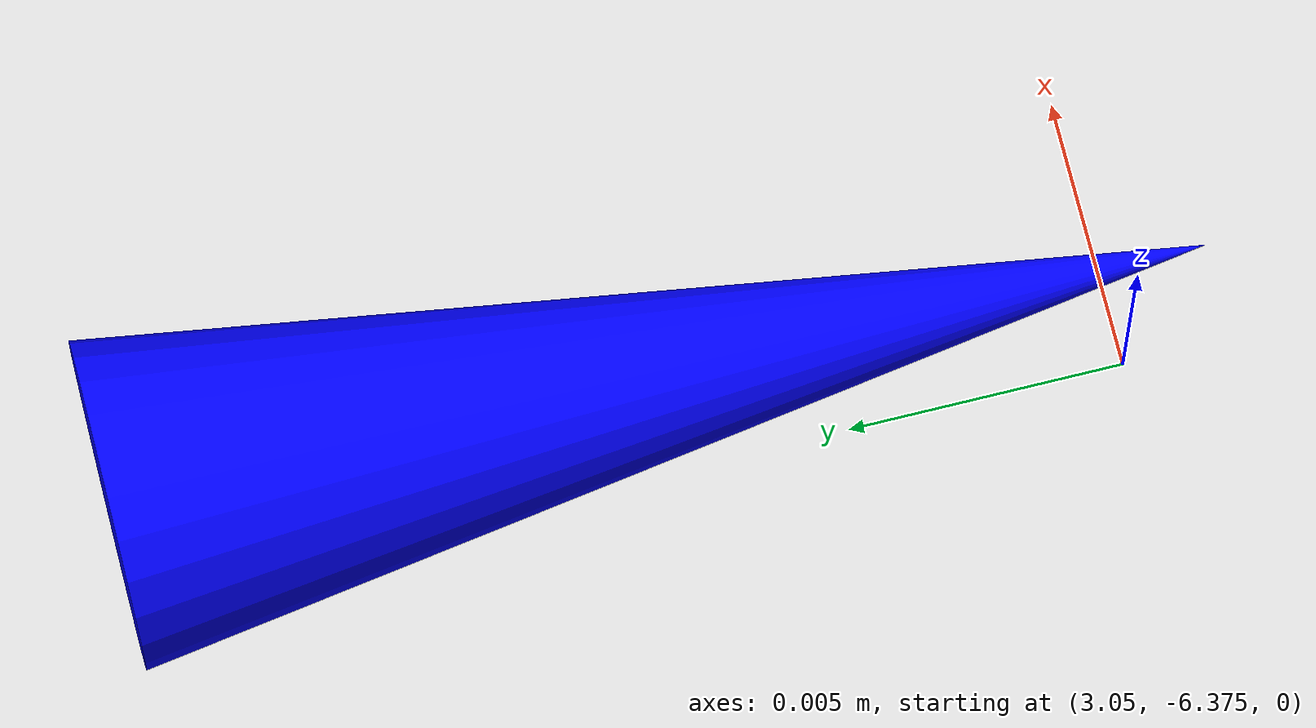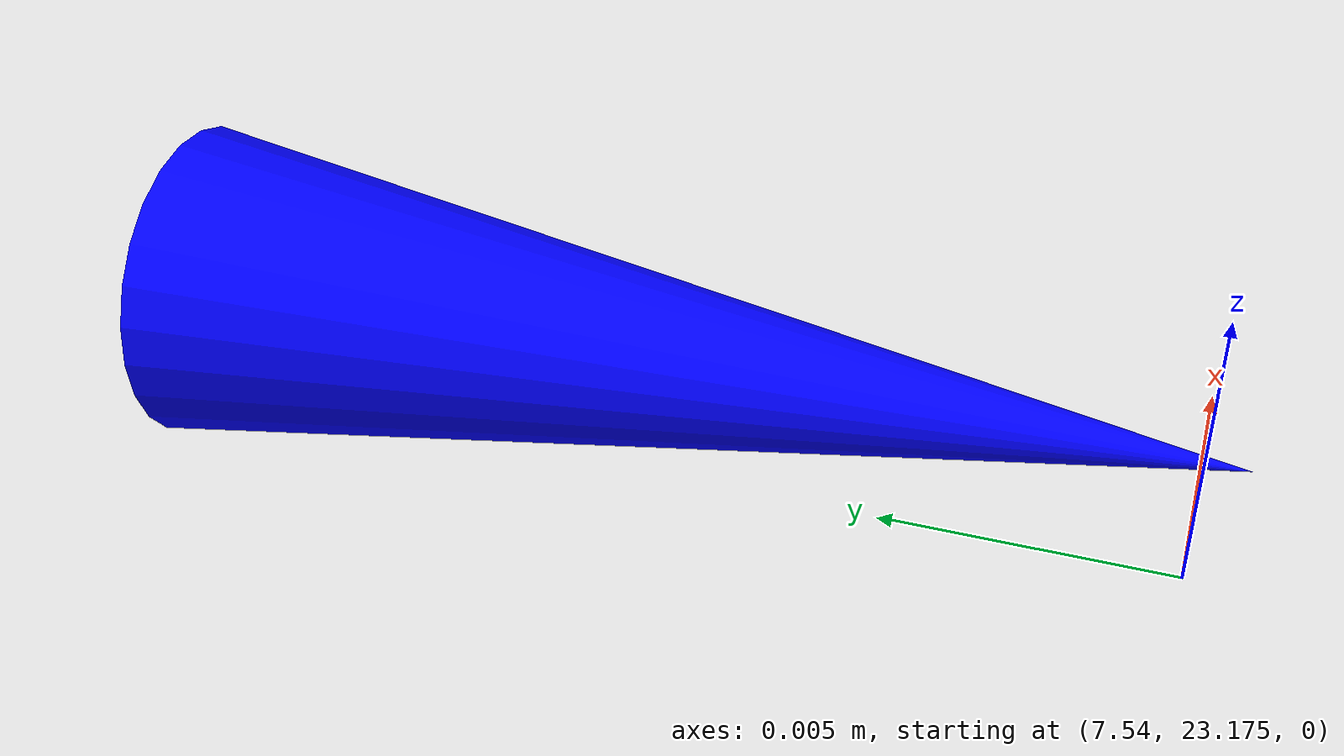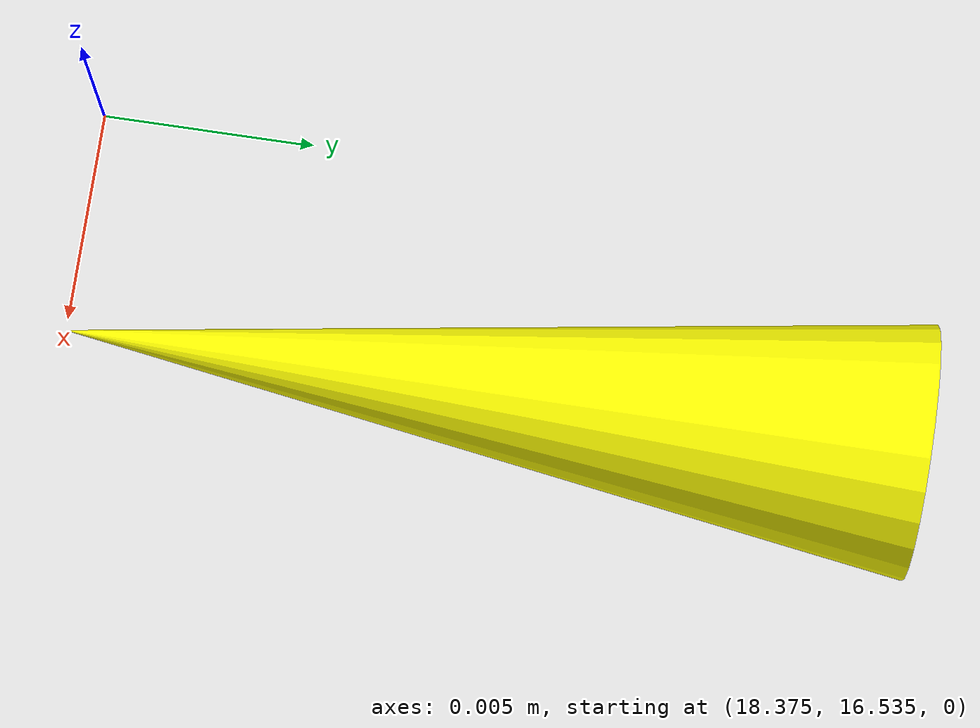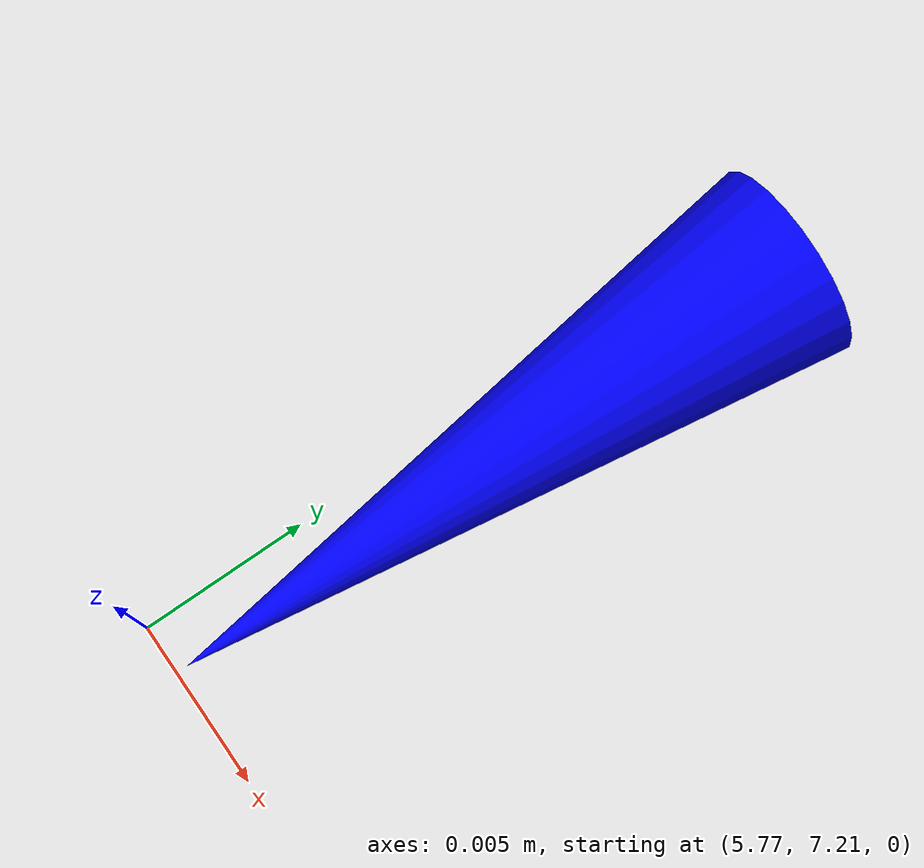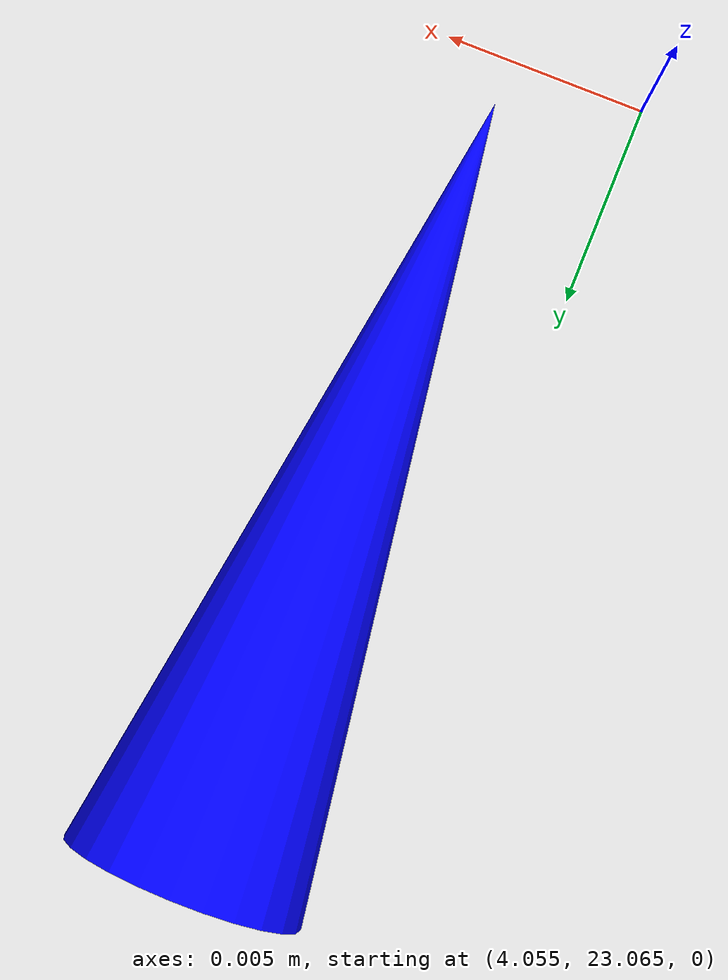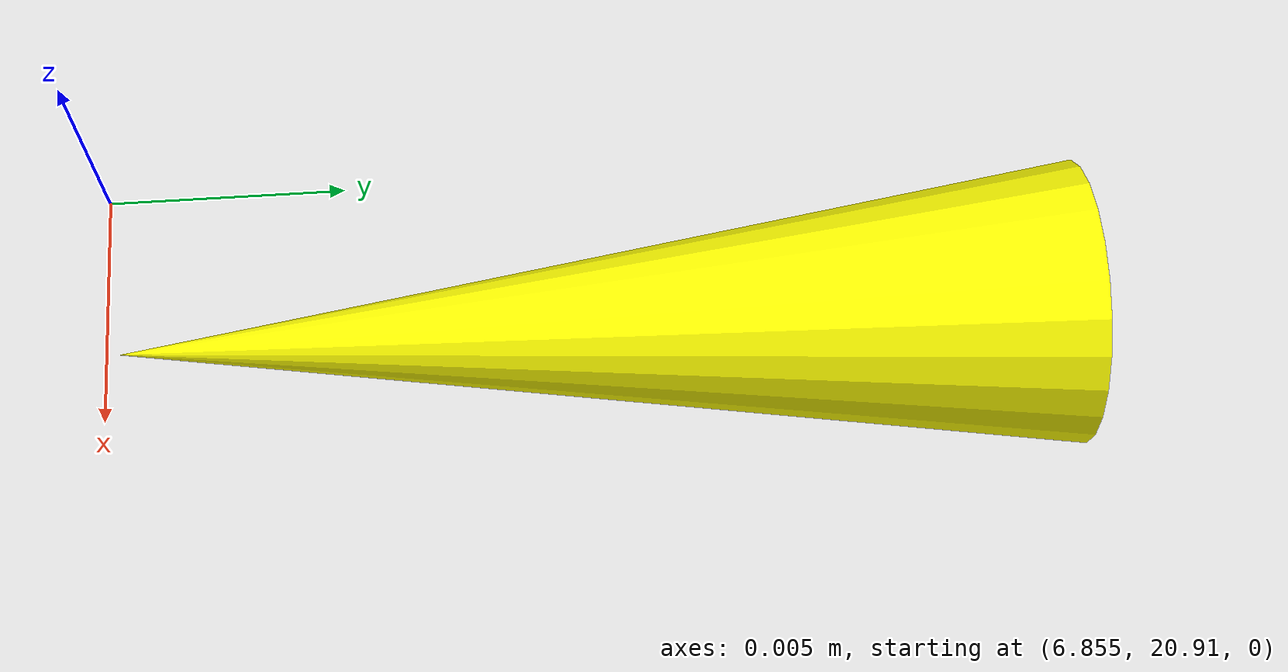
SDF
<?xml version="1.0"?>
  <sdf version='1.9'>
     <model name='cone_0'>
      <link name='cone_0_link'>
        <inertial>
			<mass>0</mass>
			<inertia>
			<ixx>0.166667</ixx>
			<ixy>0</ixy>
			<ixz>0</ixz>
			<iyy>0.166667</iyy>
			<iyz>0</iyz>
			<izz>0.166667</izz>
			</inertia>
		</inertial>
        <collision name='cone_0_collision'>
          <geometry>
            <mesh>
              <uri>/models/cone/meshes/cone.stl</uri>
              <scale>0.001 0.001 0.001</scale>
            </mesh>
          </geometry>
        </collision>
        <visual name='cone_0_visual'>
          <geometry>
            <mesh>
              <uri>/models/cone/meshes/cone.stl</uri>
              <scale>0.001 0.001 0.001</scale>
            </mesh>
          </geometry>
          <material>
            <ambient>1 1 0 1</ambient>
            <diffuse>1 1 0 1</diffuse>
            <specular>1 1 0 1</specular>
          </material>
        </visual>

        <enable_wind>false</enable_wind>
      </link>
      <pose>5.461853710610571 20.88471455814839 0.0 1.57 0 0</pose>
      <static>true</static>
      </model>

     <model name='cone_1'>
      <link name='cone_1_link'>
        <inertial>
			<mass>0</mass>
			<inertia>
			<ixx>0.166667</ixx>
			<ixy>0</ixy>
			<ixz>0</ixz>
			<iyy>0.166667</iyy>
			<iyz>0</iyz>
			<izz>0.166667</izz>
			</inertia>
		</inertial>
        <collision name='cone_1_collision'>
          <geometry>
            <mesh>
              <uri>/models/cone/meshes/cone.stl</uri>
              <scale>0.001 0.001 0.001</scale>
            </mesh>
          </geometry>
        </collision>
        <visual name='cone_1_visual'>
          <geometry>
            <mesh>
              <uri>/models/cone/meshes/cone.stl</uri>
              <scale>0.001 0.001 0.001</scale>
            </mesh>
          </geometry>
          <material>
            <ambient>1 1 0 1</ambient>
            <diffuse>1 1 0 1</diffuse>
            <specular>1 1 0 1</specular>
          </material>
        </visual>

        <enable_wind>false</enable_wind>
      </link>
      <pose>6.858494923565017 20.930265685835174 0.0 1.57 0 0</pose>
      <static>true</static>
      </model>

     <model name='cone_2'>
      <link name='cone_2_link'>
        <inertial>
			<mass>0</mass>
			<inertia>
			<ixx>0.166667</ixx>
			<ixy>0</ixy>
			<ixz>0</ixz>
			<iyy>0.166667</iyy>
			<iyz>0</iyz>
			<izz>0.166667</izz>
			</inertia>
		</inertial>
        <collision name='cone_2_collision'>
          <geometry>
            <mesh>
              <uri>/models/cone/meshes/cone.stl</uri>
              <scale>0.001 0.001 0.001</scale>
            </mesh>
          </geometry>
        </collision>
        <visual name='cone_2_visual'>
          <geometry>
            <mesh>
              <uri>/models/cone/meshes/cone.stl</uri>
              <scale>0.001 0.001 0.001</scale>
            </mesh>
          </geometry>
          <material>
            <ambient>1 1 0 1</ambient>
            <diffuse>1 1 0 1</diffuse>
            <specular>1 1 0 1</specular>
          </material>
        </visual>

        <enable_wind>false</enable_wind>
      </link>
      <pose>8.249053797646212 20.972389109776337 0.0 1.57 0 0</pose>
      <static>true</static>
      </model>

     <model name='cone_3'>
      <link name='cone_3_link'>
        <inertial>
			<mass>0</mass>
			<inertia>
			<ixx>0.166667</ixx>
			<ixy>0</ixy>
			<ixz>0</ixz>
			<iyy>0.166667</iyy>
			<iyz>0</iyz>
			<izz>0.166667</izz>
			</inertia>
		</inertial>
        <collision name='cone_3_collision'>
          <geometry>
            <mesh>
              <uri>/models/cone/meshes/cone.stl</uri>
              <scale>0.001 0.001 0.001</scale>
            </mesh>
          </geometry>
        </collision>
        <visual name='cone_3_visual'>
          <geometry>
            <mesh>
              <uri>/models/cone/meshes/cone.stl</uri>
              <scale>0.001 0.001 0.001</scale>
            </mesh>
          </geometry>
          <material>
            <ambient>1 1 0 1</ambient>
            <diffuse>1 1 0 1</diffuse>
            <specular>1 1 0 1</specular>
          </material>
        </visual>

        <enable_wind>false</enable_wind>
      </link>
      <pose>11.012488916765536 21.013946171543957 0.0 1.57 0 0</pose>
      <static>true</static>
      </model>

     <model name='cone_4'>
      <link name='cone_4_link'>
        <inertial>
			<mass>0</mass>
			<inertia>
			<ixx>0.166667</ixx>
			<ixy>0</ixy>
			<ixz>0</ixz>
			<iyy>0.166667</iyy>
			<iyz>0</iyz>
			<izz>0.166667</izz>
			</inertia>
		</inertial>
        <collision name='cone_4_collision'>
          <geometry>
            <mesh>
              <uri>/models/cone/meshes/cone.stl</uri>
              <scale>0.001 0.001 0.001</scale>
            </mesh>
          </geometry>
        </collision>
        <visual name='cone_4_visual'>
          <geometry>
            <mesh>
              <uri>/models/cone/meshes/cone.stl</uri>
              <scale>0.001 0.001 0.001</scale>
            </mesh>
          </geometry>
          <material>
            <ambient>1 1 0 1</ambient>
            <diffuse>1 1 0 1</diffuse>
            <specular>1 1 0 1</specular>
          </material>
        </visual>

        <enable_wind>false</enable_wind>
      </link>
      <pose>12.385001433253166 20.99744425659682 0.0 1.57 0 0</pose>
      <static>true</static>
      </model>

     <model name='cone_5'>
      <link name='cone_5_link'>
        <inertial>
			<mass>0</mass>
			<inertia>
			<ixx>0.166667</ixx>
			<ixy>0</ixy>
			<ixz>0</ixz>
			<iyy>0.166667</iyy>
			<iyz>0</iyz>
			<izz>0.166667</izz>
			</inertia>
		</inertial>
        <collision name='cone_5_collision'>
          <geometry>
            <mesh>
              <uri>/models/cone/meshes/cone.stl</uri>
              <scale>0.001 0.001 0.001</scale>
            </mesh>
          </geometry>
        </collision>
        <visual name='cone_5_visual'>
          <geometry>
            <mesh>
              <uri>/models/cone/meshes/cone.stl</uri>
              <scale>0.001 0.001 0.001</scale>
            </mesh>
          </geometry>
          <material>
            <ambient>1 1 0 1</ambient>
            <diffuse>1 1 0 1</diffuse>
            <specular>1 1 0 1</specular>
          </material>
        </visual>

        <enable_wind>false</enable_wind>
      </link>
      <pose>13.75042883512901 20.94566106259708 0.0 1.57 0 0</pose>
      <static>true</static>
      </model>

     <model name='cone_6'>
      <link name='cone_6_link'>
        <inertial>
			<mass>0</mass>
			<inertia>
			<ixx>0.166667</ixx>
			<ixy>0</ixy>
			<ixz>0</ixz>
			<iyy>0.166667</iyy>
			<iyz>0</iyz>
			<izz>0.166667</izz>
			</inertia>
		</inertial>
        <collision name='cone_6_collision'>
          <geometry>
            <mesh>
              <uri>/models/cone/meshes/cone.stl</uri>
              <scale>0.001 0.001 0.001</scale>
            </mesh>
          </geometry>
        </collision>
        <visual name='cone_6_visual'>
          <geometry>
            <mesh>
              <uri>/models/cone/meshes/cone.stl</uri>
              <scale>0.001 0.001 0.001</scale>
            </mesh>
          </geometry>
          <material>
            <ambient>1 1 0 1</ambient>
            <diffuse>1 1 0 1</diffuse>
            <specular>1 1 0 1</specular>
          </material>
        </visual>

        <enable_wind>false</enable_wind>
      </link>
      <pose>15.047390586279672 20.833091591517665 0.0 1.57 0 0</pose>
      <static>true</static>
      </model>

     <model name='cone_7'>
      <link name='cone_7_link'>
        <inertial>
			<mass>0</mass>
			<inertia>
			<ixx>0.166667</ixx>
			<ixy>0</ixy>
			<ixz>0</ixz>
			<iyy>0.166667</iyy>
			<iyz>0</iyz>
			<izz>0.166667</izz>
			</inertia>
		</inertial>
        <collision name='cone_7_collision'>
          <geometry>
            <mesh>
              <uri>/models/cone/meshes/cone.stl</uri>
              <scale>0.001 0.001 0.001</scale>
            </mesh>
          </geometry>
        </collision>
        <visual name='cone_7_visual'>
          <geometry>
            <mesh>
              <uri>/models/cone/meshes/cone.stl</uri>
              <scale>0.001 0.001 0.001</scale>
            </mesh>
          </geometry>
          <material>
            <ambient>1 1 0 1</ambient>
            <diffuse>1 1 0 1</diffuse>
            <specular>1 1 0 1</specular>
          </material>
        </visual>

        <enable_wind>false</enable_wind>
      </link>
      <pose>16.667568621350263 20.33320980173812 0.0 1.57 0 0</pose>
      <static>true</static>
      </model>

     <model name='cone_8'>
      <link name='cone_8_link'>
        <inertial>
			<mass>0</mass>
			<inertia>
			<ixx>0.166667</ixx>
			<ixy>0</ixy>
			<ixz>0</ixz>
			<iyy>0.166667</iyy>
			<iyz>0</iyz>
			<izz>0.166667</izz>
			</inertia>
		</inertial>
        <collision name='cone_8_collision'>
          <geometry>
            <mesh>
              <uri>/models/cone/meshes/cone.stl</uri>
              <scale>0.001 0.001 0.001</scale>
            </mesh>
          </geometry>
        </collision>
        <visual name='cone_8_visual'>
          <geometry>
            <mesh>
              <uri>/models/cone/meshes/cone.stl</uri>
              <scale>0.001 0.001 0.001</scale>
            </mesh>
          </geometry>
          <material>
            <ambient>1 1 0 1</ambient>
            <diffuse>1 1 0 1</diffuse>
            <specular>1 1 0 1</specular>
          </material>
        </visual>

        <enable_wind>false</enable_wind>
      </link>
      <pose>17.763769055198573 19.246141535824844 0.0 1.57 0 0</pose>
      <static>true</static>
      </model>

     <model name='cone_9'>
      <link name='cone_9_link'>
        <inertial>
			<mass>0</mass>
			<inertia>
			<ixx>0.166667</ixx>
			<ixy>0</ixy>
			<ixz>0</ixz>
			<iyy>0.166667</iyy>
			<iyz>0</iyz>
			<izz>0.166667</izz>
			</inertia>
		</inertial>
        <collision name='cone_9_collision'>
          <geometry>
            <mesh>
              <uri>/models/cone/meshes/cone.stl</uri>
              <scale>0.001 0.001 0.001</scale>
            </mesh>
          </geometry>
        </collision>
        <visual name='cone_9_visual'>
          <geometry>
            <mesh>
              <uri>/models/cone/meshes/cone.stl</uri>
              <scale>0.001 0.001 0.001</scale>
            </mesh>
          </geometry>
          <material>
            <ambient>1 1 0 1</ambient>
            <diffuse>1 1 0 1</diffuse>
            <specular>1 1 0 1</specular>
          </material>
        </visual>

        <enable_wind>false</enable_wind>
      </link>
      <pose>18.21209805776642 18.218825783853802 0.0 1.57 0 0</pose>
      <static>true</static>
      </model>

     <model name='cone_10'>
      <link name='cone_10_link'>
        <inertial>
			<mass>0</mass>
			<inertia>
			<ixx>0.166667</ixx>
			<ixy>0</ixy>
			<ixz>0</ixz>
			<iyy>0.166667</iyy>
			<iyz>0</iyz>
			<izz>0.166667</izz>
			</inertia>
		</inertial>
        <collision name='cone_10_collision'>
          <geometry>
            <mesh>
              <uri>/models/cone/meshes/cone.stl</uri>
              <scale>0.001 0.001 0.001</scale>
            </mesh>
          </geometry>
        </collision>
        <visual name='cone_10_visual'>
          <geometry>
            <mesh>
              <uri>/models/cone/meshes/cone.stl</uri>
              <scale>0.001 0.001 0.001</scale>
            </mesh>
          </geometry>
          <material>
            <ambient>1 1 0 1</ambient>
            <diffuse>1 1 0 1</diffuse>
            <specular>1 1 0 1</specular>
          </material>
        </visual>

        <enable_wind>false</enable_wind>
      </link>
      <pose>18.38025250731713 16.55498046160501 0.0 1.57 0 0</pose>
      <static>true</static>
      </model>

     <model name='cone_11'>
      <link name='cone_11_link'>
        <inertial>
			<mass>0</mass>
			<inertia>
			<ixx>0.166667</ixx>
			<ixy>0</ixy>
			<ixz>0</ixz>
			<iyy>0.166667</iyy>
			<iyz>0</iyz>
			<izz>0.166667</izz>
			</inertia>
		</inertial>
        <collision name='cone_11_collision'>
          <geometry>
            <mesh>
              <uri>/models/cone/meshes/cone.stl</uri>
              <scale>0.001 0.001 0.001</scale>
            </mesh>
          </geometry>
        </collision>
        <visual name='cone_11_visual'>
          <geometry>
            <mesh>
              <uri>/models/cone/meshes/cone.stl</uri>
              <scale>0.001 0.001 0.001</scale>
            </mesh>
          </geometry>
          <material>
            <ambient>1 1 0 1</ambient>
            <diffuse>1 1 0 1</diffuse>
            <specular>1 1 0 1</specular>
          </material>
        </visual>

        <enable_wind>false</enable_wind>
      </link>
      <pose>18.111856943490636 15.518942309492022 0.0 1.57 0 0</pose>
      <static>true</static>
      </model>

     <model name='cone_12'>
      <link name='cone_12_link'>
        <inertial>
			<mass>0</mass>
			<inertia>
			<ixx>0.166667</ixx>
			<ixy>0</ixy>
			<ixz>0</ixz>
			<iyy>0.166667</iyy>
			<iyz>0</iyz>
			<izz>0.166667</izz>
			</inertia>
		</inertial>
        <collision name='cone_12_collision'>
          <geometry>
            <mesh>
              <uri>/models/cone/meshes/cone.stl</uri>
              <scale>0.001 0.001 0.001</scale>
            </mesh>
          </geometry>
        </collision>
        <visual name='cone_12_visual'>
          <geometry>
            <mesh>
              <uri>/models/cone/meshes/cone.stl</uri>
              <scale>0.001 0.001 0.001</scale>
            </mesh>
          </geometry>
          <material>
            <ambient>1 1 0 1</ambient>
            <diffuse>1 1 0 1</diffuse>
            <specular>1 1 0 1</specular>
          </material>
        </visual>

        <enable_wind>false</enable_wind>
      </link>
      <pose>17.136057229341134 14.211767340198229 0.0 1.57 0 0</pose>
      <static>true</static>
      </model>

     <model name='cone_13'>
      <link name='cone_13_link'>
        <inertial>
			<mass>0</mass>
			<inertia>
			<ixx>0.166667</ixx>
			<ixy>0</ixy>
			<ixz>0</ixz>
			<iyy>0.166667</iyy>
			<iyz>0</iyz>
			<izz>0.166667</izz>
			</inertia>
		</inertial>
        <collision name='cone_13_collision'>
          <geometry>
            <mesh>
              <uri>/models/cone/meshes/cone.stl</uri>
              <scale>0.001 0.001 0.001</scale>
            </mesh>
          </geometry>
        </collision>
        <visual name='cone_13_visual'>
          <geometry>
            <mesh>
              <uri>/models/cone/meshes/cone.stl</uri>
              <scale>0.001 0.001 0.001</scale>
            </mesh>
          </geometry>
          <material>
            <ambient>1 1 0 1</ambient>
            <diffuse>1 1 0 1</diffuse>
            <specular>1 1 0 1</specular>
          </material>
        </visual>

        <enable_wind>false</enable_wind>
      </link>
      <pose>15.664144885457366 13.274260054187828 0.0 1.57 0 0</pose>
      <static>true</static>
      </model>

     <model name='cone_14'>
      <link name='cone_14_link'>
        <inertial>
			<mass>0</mass>
			<inertia>
			<ixx>0.166667</ixx>
			<ixy>0</ixy>
			<ixz>0</ixz>
			<iyy>0.166667</iyy>
			<iyz>0</iyz>
			<izz>0.166667</izz>
			</inertia>
		</inertial>
        <collision name='cone_14_collision'>
          <geometry>
            <mesh>
              <uri>/models/cone/meshes/cone.stl</uri>
              <scale>0.001 0.001 0.001</scale>
            </mesh>
          </geometry>
        </collision>
        <visual name='cone_14_visual'>
          <geometry>
            <mesh>
              <uri>/models/cone/meshes/cone.stl</uri>
              <scale>0.001 0.001 0.001</scale>
            </mesh>
          </geometry>
          <material>
            <ambient>1 1 0 1</ambient>
            <diffuse>1 1 0 1</diffuse>
            <specular>1 1 0 1</specular>
          </material>
        </visual>

        <enable_wind>false</enable_wind>
      </link>
      <pose>14.567884065774455 12.950934992118238 0.0 1.57 0 0</pose>
      <static>true</static>
      </model>

     <model name='cone_15'>
      <link name='cone_15_link'>
        <inertial>
			<mass>0</mass>
			<inertia>
			<ixx>0.166667</ixx>
			<ixy>0</ixy>
			<ixz>0</ixz>
			<iyy>0.166667</iyy>
			<iyz>0</iyz>
			<izz>0.166667</izz>
			</inertia>
		</inertial>
        <collision name='cone_15_collision'>
          <geometry>
            <mesh>
              <uri>/models/cone/meshes/cone.stl</uri>
              <scale>0.001 0.001 0.001</scale>
            </mesh>
          </geometry>
        </collision>
        <visual name='cone_15_visual'>
          <geometry>
            <mesh>
              <uri>/models/cone/meshes/cone.stl</uri>
              <scale>0.001 0.001 0.001</scale>
            </mesh>
          </geometry>
          <material>
            <ambient>1 1 0 1</ambient>
            <diffuse>1 1 0 1</diffuse>
            <specular>1 1 0 1</specular>
          </material>
        </visual>

        <enable_wind>false</enable_wind>
      </link>
      <pose>13.445545527391472 12.910194791111978 0.0 1.57 0 0</pose>
      <static>true</static>
      </model>

     <model name='cone_16'>
      <link name='cone_16_link'>
        <inertial>
			<mass>0</mass>
			<inertia>
			<ixx>0.166667</ixx>
			<ixy>0</ixy>
			<ixz>0</ixz>
			<iyy>0.166667</iyy>
			<iyz>0</iyz>
			<izz>0.166667</izz>
			</inertia>
		</inertial>
        <collision name='cone_16_collision'>
          <geometry>
            <mesh>
              <uri>/models/cone/meshes/cone.stl</uri>
              <scale>0.001 0.001 0.001</scale>
            </mesh>
          </geometry>
        </collision>
        <visual name='cone_16_visual'>
          <geometry>
            <mesh>
              <uri>/models/cone/meshes/cone.stl</uri>
              <scale>0.001 0.001 0.001</scale>
            </mesh>
          </geometry>
          <material>
            <ambient>1 1 0 1</ambient>
            <diffuse>1 1 0 1</diffuse>
            <specular>1 1 0 1</specular>
          </material>
        </visual>

        <enable_wind>false</enable_wind>
      </link>
      <pose>11.755357576907851 13.366073181148977 0.0 1.57 0 0</pose>
      <static>true</static>
      </model>

     <model name='cone_17'>
      <link name='cone_17_link'>
        <inertial>
			<mass>0</mass>
			<inertia>
			<ixx>0.166667</ixx>
			<ixy>0</ixy>
			<ixz>0</ixz>
			<iyy>0.166667</iyy>
			<iyz>0</iyz>
			<izz>0.166667</izz>
			</inertia>
		</inertial>
        <collision name='cone_17_collision'>
          <geometry>
            <mesh>
              <uri>/models/cone/meshes/cone.stl</uri>
              <scale>0.001 0.001 0.001</scale>
            </mesh>
          </geometry>
        </collision>
        <visual name='cone_17_visual'>
          <geometry>
            <mesh>
              <uri>/models/cone/meshes/cone.stl</uri>
              <scale>0.001 0.001 0.001</scale>
            </mesh>
          </geometry>
          <material>
            <ambient>1 1 0 1</ambient>
            <diffuse>1 1 0 1</diffuse>
            <specular>1 1 0 1</specular>
          </material>
        </visual>

        <enable_wind>false</enable_wind>
      </link>
      <pose>10.121315170619077 14.318226993721737 0.0 1.57 0 0</pose>
      <static>true</static>
      </model>

     <model name='cone_18'>
      <link name='cone_18_link'>
        <inertial>
			<mass>0</mass>
			<inertia>
			<ixx>0.166667</ixx>
			<ixy>0</ixy>
			<ixz>0</ixz>
			<iyy>0.166667</iyy>
			<iyz>0</iyz>
			<izz>0.166667</izz>
			</inertia>
		</inertial>
        <collision name='cone_18_collision'>
          <geometry>
            <mesh>
              <uri>/models/cone/meshes/cone.stl</uri>
              <scale>0.001 0.001 0.001</scale>
            </mesh>
          </geometry>
        </collision>
        <visual name='cone_18_visual'>
          <geometry>
            <mesh>
              <uri>/models/cone/meshes/cone.stl</uri>
              <scale>0.001 0.001 0.001</scale>
            </mesh>
          </geometry>
          <material>
            <ambient>1 1 0 1</ambient>
            <diffuse>1 1 0 1</diffuse>
            <specular>1 1 0 1</specular>
          </material>
        </visual>

        <enable_wind>false</enable_wind>
      </link>
      <pose>8.974002374208737 15.123328026821842 0.0 1.57 0 0</pose>
      <static>true</static>
      </model>

     <model name='cone_19'>
      <link name='cone_19_link'>
        <inertial>
			<mass>0</mass>
			<inertia>
			<ixx>0.166667</ixx>
			<ixy>0</ixy>
			<ixz>0</ixz>
			<iyy>0.166667</iyy>
			<iyz>0</iyz>
			<izz>0.166667</izz>
			</inertia>
		</inertial>
        <collision name='cone_19_collision'>
          <geometry>
            <mesh>
              <uri>/models/cone/meshes/cone.stl</uri>
              <scale>0.001 0.001 0.001</scale>
            </mesh>
          </geometry>
        </collision>
        <visual name='cone_19_visual'>
          <geometry>
            <mesh>
              <uri>/models/cone/meshes/cone.stl</uri>
              <scale>0.001 0.001 0.001</scale>
            </mesh>
          </geometry>
          <material>
            <ambient>1 1 0 1</ambient>
            <diffuse>1 1 0 1</diffuse>
            <specular>1 1 0 1</specular>
          </material>
        </visual>

        <enable_wind>false</enable_wind>
      </link>
      <pose>6.953604428393607 16.255397786791626 0.0 1.57 0 0</pose>
      <static>true</static>
      </model>

     <model name='cone_20'>
      <link name='cone_20_link'>
        <inertial>
			<mass>0</mass>
			<inertia>
			<ixx>0.166667</ixx>
			<ixy>0</ixy>
			<ixz>0</ixz>
			<iyy>0.166667</iyy>
			<iyz>0</iyz>
			<izz>0.166667</izz>
			</inertia>
		</inertial>
        <collision name='cone_20_collision'>
          <geometry>
            <mesh>
              <uri>/models/cone/meshes/cone.stl</uri>
              <scale>0.001 0.001 0.001</scale>
            </mesh>
          </geometry>
        </collision>
        <visual name='cone_20_visual'>
          <geometry>
            <mesh>
              <uri>/models/cone/meshes/cone.stl</uri>
              <scale>0.001 0.001 0.001</scale>
            </mesh>
          </geometry>
          <material>
            <ambient>1 1 0 1</ambient>
            <diffuse>1 1 0 1</diffuse>
            <specular>1 1 0 1</specular>
          </material>
        </visual>

        <enable_wind>false</enable_wind>
      </link>
      <pose>5.418184121538784 16.707318278228485 0.0 1.57 0 0</pose>
      <static>true</static>
      </model>

     <model name='cone_21'>
      <link name='cone_21_link'>
        <inertial>
			<mass>0</mass>
			<inertia>
			<ixx>0.166667</ixx>
			<ixy>0</ixy>
			<ixz>0</ixz>
			<iyy>0.166667</iyy>
			<iyz>0</iyz>
			<izz>0.166667</izz>
			</inertia>
		</inertial>
        <collision name='cone_21_collision'>
          <geometry>
            <mesh>
              <uri>/models/cone/meshes/cone.stl</uri>
              <scale>0.001 0.001 0.001</scale>
            </mesh>
          </geometry>
        </collision>
        <visual name='cone_21_visual'>
          <geometry>
            <mesh>
              <uri>/models/cone/meshes/cone.stl</uri>
              <scale>0.001 0.001 0.001</scale>
            </mesh>
          </geometry>
          <material>
            <ambient>1 1 0 1</ambient>
            <diffuse>1 1 0 1</diffuse>
            <specular>1 1 0 1</specular>
          </material>
        </visual>

        <enable_wind>false</enable_wind>
      </link>
      <pose>3.0466980333808897 16.828615857836233 0.0 1.57 0 0</pose>
      <static>true</static>
      </model>

     <model name='cone_22'>
      <link name='cone_22_link'>
        <inertial>
			<mass>0</mass>
			<inertia>
			<ixx>0.166667</ixx>
			<ixy>0</ixy>
			<ixz>0</ixz>
			<iyy>0.166667</iyy>
			<iyz>0</iyz>
			<izz>0.166667</izz>
			</inertia>
		</inertial>
        <collision name='cone_22_collision'>
          <geometry>
            <mesh>
              <uri>/models/cone/meshes/cone.stl</uri>
              <scale>0.001 0.001 0.001</scale>
            </mesh>
          </geometry>
        </collision>
        <visual name='cone_22_visual'>
          <geometry>
            <mesh>
              <uri>/models/cone/meshes/cone.stl</uri>
              <scale>0.001 0.001 0.001</scale>
            </mesh>
          </geometry>
          <material>
            <ambient>1 1 0 1</ambient>
            <diffuse>1 1 0 1</diffuse>
            <specular>1 1 0 1</specular>
          </material>
        </visual>

        <enable_wind>false</enable_wind>
      </link>
      <pose>0.5531739046420245 15.993148931849637 0.0 1.57 0 0</pose>
      <static>true</static>
      </model>

     <model name='cone_23'>
      <link name='cone_23_link'>
        <inertial>
			<mass>0</mass>
			<inertia>
			<ixx>0.166667</ixx>
			<ixy>0</ixy>
			<ixz>0</ixz>
			<iyy>0.166667</iyy>
			<iyz>0</iyz>
			<izz>0.166667</izz>
			</inertia>
		</inertial>
        <collision name='cone_23_collision'>
          <geometry>
            <mesh>
              <uri>/models/cone/meshes/cone.stl</uri>
              <scale>0.001 0.001 0.001</scale>
            </mesh>
          </geometry>
        </collision>
        <visual name='cone_23_visual'>
          <geometry>
            <mesh>
              <uri>/models/cone/meshes/cone.stl</uri>
              <scale>0.001 0.001 0.001</scale>
            </mesh>
          </geometry>
          <material>
            <ambient>1 1 0 1</ambient>
            <diffuse>1 1 0 1</diffuse>
            <specular>1 1 0 1</specular>
          </material>
        </visual>

        <enable_wind>false</enable_wind>
      </link>
      <pose>-0.660070594904723 14.481724441493718 0.0 1.57 0 0</pose>
      <static>true</static>
      </model>

     <model name='cone_24'>
      <link name='cone_24_link'>
        <inertial>
			<mass>0</mass>
			<inertia>
			<ixx>0.166667</ixx>
			<ixy>0</ixy>
			<ixz>0</ixz>
			<iyy>0.166667</iyy>
			<iyz>0</iyz>
			<izz>0.166667</izz>
			</inertia>
		</inertial>
        <collision name='cone_24_collision'>
          <geometry>
            <mesh>
              <uri>/models/cone/meshes/cone.stl</uri>
              <scale>0.001 0.001 0.001</scale>
            </mesh>
          </geometry>
        </collision>
        <visual name='cone_24_visual'>
          <geometry>
            <mesh>
              <uri>/models/cone/meshes/cone.stl</uri>
              <scale>0.001 0.001 0.001</scale>
            </mesh>
          </geometry>
          <material>
            <ambient>1 1 0 1</ambient>
            <diffuse>1 1 0 1</diffuse>
            <specular>1 1 0 1</specular>
          </material>
        </visual>

        <enable_wind>false</enable_wind>
      </link>
      <pose>-0.9393057502952074 12.579556270952267 0.0 1.57 0 0</pose>
      <static>true</static>
      </model>

     <model name='cone_25'>
      <link name='cone_25_link'>
        <inertial>
			<mass>0</mass>
			<inertia>
			<ixx>0.166667</ixx>
			<ixy>0</ixy>
			<ixz>0</ixz>
			<iyy>0.166667</iyy>
			<iyz>0</iyz>
			<izz>0.166667</izz>
			</inertia>
		</inertial>
        <collision name='cone_25_collision'>
          <geometry>
            <mesh>
              <uri>/models/cone/meshes/cone.stl</uri>
              <scale>0.001 0.001 0.001</scale>
            </mesh>
          </geometry>
        </collision>
        <visual name='cone_25_visual'>
          <geometry>
            <mesh>
              <uri>/models/cone/meshes/cone.stl</uri>
              <scale>0.001 0.001 0.001</scale>
            </mesh>
          </geometry>
          <material>
            <ambient>1 1 0 1</ambient>
            <diffuse>1 1 0 1</diffuse>
            <specular>1 1 0 1</specular>
          </material>
        </visual>

        <enable_wind>false</enable_wind>
      </link>
      <pose>-0.25636574404422685 10.801382537185802 0.0 1.57 0 0</pose>
      <static>true</static>
      </model>

     <model name='cone_26'>
      <link name='cone_26_link'>
        <inertial>
			<mass>0</mass>
			<inertia>
			<ixx>0.166667</ixx>
			<ixy>0</ixy>
			<ixz>0</ixz>
			<iyy>0.166667</iyy>
			<iyz>0</iyz>
			<izz>0.166667</izz>
			</inertia>
		</inertial>
        <collision name='cone_26_collision'>
          <geometry>
            <mesh>
              <uri>/models/cone/meshes/cone.stl</uri>
              <scale>0.001 0.001 0.001</scale>
            </mesh>
          </geometry>
        </collision>
        <visual name='cone_26_visual'>
          <geometry>
            <mesh>
              <uri>/models/cone/meshes/cone.stl</uri>
              <scale>0.001 0.001 0.001</scale>
            </mesh>
          </geometry>
          <material>
            <ambient>1 1 0 1</ambient>
            <diffuse>1 1 0 1</diffuse>
            <specular>1 1 0 1</specular>
          </material>
        </visual>

        <enable_wind>false</enable_wind>
      </link>
      <pose>2.261912192911579 8.843992821543827 0.0 1.57 0 0</pose>
      <static>true</static>
      </model>

     <model name='cone_27'>
      <link name='cone_27_link'>
        <inertial>
			<mass>0</mass>
			<inertia>
			<ixx>0.166667</ixx>
			<ixy>0</ixy>
			<ixz>0</ixz>
			<iyy>0.166667</iyy>
			<iyz>0</iyz>
			<izz>0.166667</izz>
			</inertia>
		</inertial>
        <collision name='cone_27_collision'>
          <geometry>
            <mesh>
              <uri>/models/cone/meshes/cone.stl</uri>
              <scale>0.001 0.001 0.001</scale>
            </mesh>
          </geometry>
        </collision>
        <visual name='cone_27_visual'>
          <geometry>
            <mesh>
              <uri>/models/cone/meshes/cone.stl</uri>
              <scale>0.001 0.001 0.001</scale>
            </mesh>
          </geometry>
          <material>
            <ambient>1 1 0 1</ambient>
            <diffuse>1 1 0 1</diffuse>
            <specular>1 1 0 1</specular>
          </material>
        </visual>

        <enable_wind>false</enable_wind>
      </link>
      <pose>3.140082706298878 8.170682581768297 0.0 1.57 0 0</pose>
      <static>true</static>
      </model>

     <model name='cone_28'>
      <link name='cone_28_link'>
        <inertial>
			<mass>0</mass>
			<inertia>
			<ixx>0.166667</ixx>
			<ixy>0</ixy>
			<ixz>0</ixz>
			<iyy>0.166667</iyy>
			<iyz>0</iyz>
			<izz>0.166667</izz>
			</inertia>
		</inertial>
        <collision name='cone_28_collision'>
          <geometry>
            <mesh>
              <uri>/models/cone/meshes/cone.stl</uri>
              <scale>0.001 0.001 0.001</scale>
            </mesh>
          </geometry>
        </collision>
        <visual name='cone_28_visual'>
          <geometry>
            <mesh>
              <uri>/models/cone/meshes/cone.stl</uri>
              <scale>0.001 0.001 0.001</scale>
            </mesh>
          </geometry>
          <material>
            <ambient>1 1 0 1</ambient>
            <diffuse>1 1 0 1</diffuse>
            <specular>1 1 0 1</specular>
          </material>
        </visual>

        <enable_wind>false</enable_wind>
      </link>
      <pose>3.541752051548495 7.417095576543513 0.0 1.57 0 0</pose>
      <static>true</static>
      </model>

     <model name='cone_29'>
      <link name='cone_29_link'>
        <inertial>
			<mass>0</mass>
			<inertia>
			<ixx>0.166667</ixx>
			<ixy>0</ixy>
			<ixz>0</ixz>
			<iyy>0.166667</iyy>
			<iyz>0</iyz>
			<izz>0.166667</izz>
			</inertia>
		</inertial>
        <collision name='cone_29_collision'>
          <geometry>
            <mesh>
              <uri>/models/cone/meshes/cone.stl</uri>
              <scale>0.001 0.001 0.001</scale>
            </mesh>
          </geometry>
        </collision>
        <visual name='cone_29_visual'>
          <geometry>
            <mesh>
              <uri>/models/cone/meshes/cone.stl</uri>
              <scale>0.001 0.001 0.001</scale>
            </mesh>
          </geometry>
          <material>
            <ambient>1 1 0 1</ambient>
            <diffuse>1 1 0 1</diffuse>
            <specular>1 1 0 1</specular>
          </material>
        </visual>

        <enable_wind>false</enable_wind>
      </link>
      <pose>3.7864827911884515 5.400545177298743 0.0 1.57 0 0</pose>
      <static>true</static>
      </model>

     <model name='cone_30'>
      <link name='cone_30_link'>
        <inertial>
			<mass>0</mass>
			<inertia>
			<ixx>0.166667</ixx>
			<ixy>0</ixy>
			<ixz>0</ixz>
			<iyy>0.166667</iyy>
			<iyz>0</iyz>
			<izz>0.166667</izz>
			</inertia>
		</inertial>
        <collision name='cone_30_collision'>
          <geometry>
            <mesh>
              <uri>/models/cone/meshes/cone.stl</uri>
              <scale>0.001 0.001 0.001</scale>
            </mesh>
          </geometry>
        </collision>
        <visual name='cone_30_visual'>
          <geometry>
            <mesh>
              <uri>/models/cone/meshes/cone.stl</uri>
              <scale>0.001 0.001 0.001</scale>
            </mesh>
          </geometry>
          <material>
            <ambient>1 1 0 1</ambient>
            <diffuse>1 1 0 1</diffuse>
            <specular>1 1 0 1</specular>
          </material>
        </visual>

        <enable_wind>false</enable_wind>
      </link>
      <pose>5.254204303799309 2.999250682464126 0.0 1.57 0 0</pose>
      <static>true</static>
      </model>

     <model name='cone_31'>
      <link name='cone_31_link'>
        <inertial>
			<mass>0</mass>
			<inertia>
			<ixx>0.166667</ixx>
			<ixy>0</ixy>
			<ixz>0</ixz>
			<iyy>0.166667</iyy>
			<iyz>0</iyz>
			<izz>0.166667</izz>
			</inertia>
		</inertial>
        <collision name='cone_31_collision'>
          <geometry>
            <mesh>
              <uri>/models/cone/meshes/cone.stl</uri>
              <scale>0.001 0.001 0.001</scale>
            </mesh>
          </geometry>
        </collision>
        <visual name='cone_31_visual'>
          <geometry>
            <mesh>
              <uri>/models/cone/meshes/cone.stl</uri>
              <scale>0.001 0.001 0.001</scale>
            </mesh>
          </geometry>
          <material>
            <ambient>1 1 0 1</ambient>
            <diffuse>1 1 0 1</diffuse>
            <specular>1 1 0 1</specular>
          </material>
        </visual>

        <enable_wind>false</enable_wind>
      </link>
      <pose>6.832585765624931 2.2423744287114493 0.0 1.57 0 0</pose>
      <static>true</static>
      </model>

     <model name='cone_32'>
      <link name='cone_32_link'>
        <inertial>
			<mass>0</mass>
			<inertia>
			<ixx>0.166667</ixx>
			<ixy>0</ixy>
			<ixz>0</ixz>
			<iyy>0.166667</iyy>
			<iyz>0</iyz>
			<izz>0.166667</izz>
			</inertia>
		</inertial>
        <collision name='cone_32_collision'>
          <geometry>
            <mesh>
              <uri>/models/cone/meshes/cone.stl</uri>
              <scale>0.001 0.001 0.001</scale>
            </mesh>
          </geometry>
        </collision>
        <visual name='cone_32_visual'>
          <geometry>
            <mesh>
              <uri>/models/cone/meshes/cone.stl</uri>
              <scale>0.001 0.001 0.001</scale>
            </mesh>
          </geometry>
          <material>
            <ambient>1 1 0 1</ambient>
            <diffuse>1 1 0 1</diffuse>
            <specular>1 1 0 1</specular>
          </material>
        </visual>

        <enable_wind>false</enable_wind>
      </link>
      <pose>9.020208596699767 1.8263559609996083 0.0 1.57 0 0</pose>
      <static>true</static>
      </model>

     <model name='cone_33'>
      <link name='cone_33_link'>
        <inertial>
			<mass>0</mass>
			<inertia>
			<ixx>0.166667</ixx>
			<ixy>0</ixy>
			<ixz>0</ixz>
			<iyy>0.166667</iyy>
			<iyz>0</iyz>
			<izz>0.166667</izz>
			</inertia>
		</inertial>
        <collision name='cone_33_collision'>
          <geometry>
            <mesh>
              <uri>/models/cone/meshes/cone.stl</uri>
              <scale>0.001 0.001 0.001</scale>
            </mesh>
          </geometry>
        </collision>
        <visual name='cone_33_visual'>
          <geometry>
            <mesh>
              <uri>/models/cone/meshes/cone.stl</uri>
              <scale>0.001 0.001 0.001</scale>
            </mesh>
          </geometry>
          <material>
            <ambient>1 1 0 1</ambient>
            <diffuse>1 1 0 1</diffuse>
            <specular>1 1 0 1</specular>
          </material>
        </visual>

        <enable_wind>false</enable_wind>
      </link>
      <pose>10.276764076062062 1.554516188918564 0.0 1.57 0 0</pose>
      <static>true</static>
      </model>

     <model name='cone_34'>
      <link name='cone_34_link'>
        <inertial>
			<mass>0</mass>
			<inertia>
			<ixx>0.166667</ixx>
			<ixy>0</ixy>
			<ixz>0</ixz>
			<iyy>0.166667</iyy>
			<iyz>0</iyz>
			<izz>0.166667</izz>
			</inertia>
		</inertial>
        <collision name='cone_34_collision'>
          <geometry>
            <mesh>
              <uri>/models/cone/meshes/cone.stl</uri>
              <scale>0.001 0.001 0.001</scale>
            </mesh>
          </geometry>
        </collision>
        <visual name='cone_34_visual'>
          <geometry>
            <mesh>
              <uri>/models/cone/meshes/cone.stl</uri>
              <scale>0.001 0.001 0.001</scale>
            </mesh>
          </geometry>
          <material>
            <ambient>1 1 0 1</ambient>
            <diffuse>1 1 0 1</diffuse>
            <specular>1 1 0 1</specular>
          </material>
        </visual>

        <enable_wind>false</enable_wind>
      </link>
      <pose>11.516635595804615 1.1538011632190077 0.0 1.57 0 0</pose>
      <static>true</static>
      </model>

     <model name='cone_35'>
      <link name='cone_35_link'>
        <inertial>
			<mass>0</mass>
			<inertia>
			<ixx>0.166667</ixx>
			<ixy>0</ixy>
			<ixz>0</ixz>
			<iyy>0.166667</iyy>
			<iyz>0</iyz>
			<izz>0.166667</izz>
			</inertia>
		</inertial>
        <collision name='cone_35_collision'>
          <geometry>
            <mesh>
              <uri>/models/cone/meshes/cone.stl</uri>
              <scale>0.001 0.001 0.001</scale>
            </mesh>
          </geometry>
        </collision>
        <visual name='cone_35_visual'>
          <geometry>
            <mesh>
              <uri>/models/cone/meshes/cone.stl</uri>
              <scale>0.001 0.001 0.001</scale>
            </mesh>
          </geometry>
          <material>
            <ambient>1 1 0 1</ambient>
            <diffuse>1 1 0 1</diffuse>
            <specular>1 1 0 1</specular>
          </material>
        </visual>

        <enable_wind>false</enable_wind>
      </link>
      <pose>13.957645401589657 0.06735368541174402 0.0 1.57 0 0</pose>
      <static>true</static>
      </model>

     <model name='cone_36'>
      <link name='cone_36_link'>
        <inertial>
			<mass>0</mass>
			<inertia>
			<ixx>0.166667</ixx>
			<ixy>0</ixy>
			<ixz>0</ixz>
			<iyy>0.166667</iyy>
			<iyz>0</iyz>
			<izz>0.166667</izz>
			</inertia>
		</inertial>
        <collision name='cone_36_collision'>
          <geometry>
            <mesh>
              <uri>/models/cone/meshes/cone.stl</uri>
              <scale>0.001 0.001 0.001</scale>
            </mesh>
          </geometry>
        </collision>
        <visual name='cone_36_visual'>
          <geometry>
            <mesh>
              <uri>/models/cone/meshes/cone.stl</uri>
              <scale>0.001 0.001 0.001</scale>
            </mesh>
          </geometry>
          <material>
            <ambient>1 1 0 1</ambient>
            <diffuse>1 1 0 1</diffuse>
            <specular>1 1 0 1</specular>
          </material>
        </visual>

        <enable_wind>false</enable_wind>
      </link>
      <pose>15.015209532665274 -0.5547278206758381 0.0 1.57 0 0</pose>
      <static>true</static>
      </model>

     <model name='cone_37'>
      <link name='cone_37_link'>
        <inertial>
			<mass>0</mass>
			<inertia>
			<ixx>0.166667</ixx>
			<ixy>0</ixy>
			<ixz>0</ixz>
			<iyy>0.166667</iyy>
			<iyz>0</iyz>
			<izz>0.166667</izz>
			</inertia>
		</inertial>
        <collision name='cone_37_collision'>
          <geometry>
            <mesh>
              <uri>/models/cone/meshes/cone.stl</uri>
              <scale>0.001 0.001 0.001</scale>
            </mesh>
          </geometry>
        </collision>
        <visual name='cone_37_visual'>
          <geometry>
            <mesh>
              <uri>/models/cone/meshes/cone.stl</uri>
              <scale>0.001 0.001 0.001</scale>
            </mesh>
          </geometry>
          <material>
            <ambient>1 1 0 1</ambient>
            <diffuse>1 1 0 1</diffuse>
            <specular>1 1 0 1</specular>
          </material>
        </visual>

        <enable_wind>false</enable_wind>
      </link>
      <pose>15.740308544598133 -1.2772115232833912 0.0 1.57 0 0</pose>
      <static>true</static>
      </model>

     <model name='cone_38'>
      <link name='cone_38_link'>
        <inertial>
			<mass>0</mass>
			<inertia>
			<ixx>0.166667</ixx>
			<ixy>0</ixy>
			<ixz>0</ixz>
			<iyy>0.166667</iyy>
			<iyz>0</iyz>
			<izz>0.166667</izz>
			</inertia>
		</inertial>
        <collision name='cone_38_collision'>
          <geometry>
            <mesh>
              <uri>/models/cone/meshes/cone.stl</uri>
              <scale>0.001 0.001 0.001</scale>
            </mesh>
          </geometry>
        </collision>
        <visual name='cone_38_visual'>
          <geometry>
            <mesh>
              <uri>/models/cone/meshes/cone.stl</uri>
              <scale>0.001 0.001 0.001</scale>
            </mesh>
          </geometry>
          <material>
            <ambient>1 1 0 1</ambient>
            <diffuse>1 1 0 1</diffuse>
            <specular>1 1 0 1</specular>
          </material>
        </visual>

        <enable_wind>false</enable_wind>
      </link>
      <pose>16.093690311206913 -2.6334312551324004 0.0 1.57 0 0</pose>
      <static>true</static>
      </model>

     <model name='cone_39'>
      <link name='cone_39_link'>
        <inertial>
			<mass>0</mass>
			<inertia>
			<ixx>0.166667</ixx>
			<ixy>0</ixy>
			<ixz>0</ixz>
			<iyy>0.166667</iyy>
			<iyz>0</iyz>
			<izz>0.166667</izz>
			</inertia>
		</inertial>
        <collision name='cone_39_collision'>
          <geometry>
            <mesh>
              <uri>/models/cone/meshes/cone.stl</uri>
              <scale>0.001 0.001 0.001</scale>
            </mesh>
          </geometry>
        </collision>
        <visual name='cone_39_visual'>
          <geometry>
            <mesh>
              <uri>/models/cone/meshes/cone.stl</uri>
              <scale>0.001 0.001 0.001</scale>
            </mesh>
          </geometry>
          <material>
            <ambient>1 1 0 1</ambient>
            <diffuse>1 1 0 1</diffuse>
            <specular>1 1 0 1</specular>
          </material>
        </visual>

        <enable_wind>false</enable_wind>
      </link>
      <pose>15.619930325861795 -4.114263912167075 0.0 1.57 0 0</pose>
      <static>true</static>
      </model>

     <model name='cone_40'>
      <link name='cone_40_link'>
        <inertial>
			<mass>0</mass>
			<inertia>
			<ixx>0.166667</ixx>
			<ixy>0</ixy>
			<ixz>0</ixz>
			<iyy>0.166667</iyy>
			<iyz>0</iyz>
			<izz>0.166667</izz>
			</inertia>
		</inertial>
        <collision name='cone_40_collision'>
          <geometry>
            <mesh>
              <uri>/models/cone/meshes/cone.stl</uri>
              <scale>0.001 0.001 0.001</scale>
            </mesh>
          </geometry>
        </collision>
        <visual name='cone_40_visual'>
          <geometry>
            <mesh>
              <uri>/models/cone/meshes/cone.stl</uri>
              <scale>0.001 0.001 0.001</scale>
            </mesh>
          </geometry>
          <material>
            <ambient>1 1 0 1</ambient>
            <diffuse>1 1 0 1</diffuse>
            <specular>1 1 0 1</specular>
          </material>
        </visual>

        <enable_wind>false</enable_wind>
      </link>
      <pose>14.944878490341042 -4.8970711316204625 0.0 1.57 0 0</pose>
      <static>true</static>
      </model>

     <model name='cone_41'>
      <link name='cone_41_link'>
        <inertial>
			<mass>0</mass>
			<inertia>
			<ixx>0.166667</ixx>
			<ixy>0</ixy>
			<ixz>0</ixz>
			<iyy>0.166667</iyy>
			<iyz>0</iyz>
			<izz>0.166667</izz>
			</inertia>
		</inertial>
        <collision name='cone_41_collision'>
          <geometry>
            <mesh>
              <uri>/models/cone/meshes/cone.stl</uri>
              <scale>0.001 0.001 0.001</scale>
            </mesh>
          </geometry>
        </collision>
        <visual name='cone_41_visual'>
          <geometry>
            <mesh>
              <uri>/models/cone/meshes/cone.stl</uri>
              <scale>0.001 0.001 0.001</scale>
            </mesh>
          </geometry>
          <material>
            <ambient>1 1 0 1</ambient>
            <diffuse>1 1 0 1</diffuse>
            <specular>1 1 0 1</specular>
          </material>
        </visual>

        <enable_wind>false</enable_wind>
      </link>
      <pose>13.556174370238756 -5.479914672176381 0.0 1.57 0 0</pose>
      <static>true</static>
      </model>

     <model name='cone_42'>
      <link name='cone_42_link'>
        <inertial>
			<mass>0</mass>
			<inertia>
			<ixx>0.166667</ixx>
			<ixy>0</ixy>
			<ixz>0</ixz>
			<iyy>0.166667</iyy>
			<iyz>0</iyz>
			<izz>0.166667</izz>
			</inertia>
		</inertial>
        <collision name='cone_42_collision'>
          <geometry>
            <mesh>
              <uri>/models/cone/meshes/cone.stl</uri>
              <scale>0.001 0.001 0.001</scale>
            </mesh>
          </geometry>
        </collision>
        <visual name='cone_42_visual'>
          <geometry>
            <mesh>
              <uri>/models/cone/meshes/cone.stl</uri>
              <scale>0.001 0.001 0.001</scale>
            </mesh>
          </geometry>
          <material>
            <ambient>1 1 0 1</ambient>
            <diffuse>1 1 0 1</diffuse>
            <specular>1 1 0 1</specular>
          </material>
        </visual>

        <enable_wind>false</enable_wind>
      </link>
      <pose>12.365196983018645 -5.513585190347355 0.0 1.57 0 0</pose>
      <static>true</static>
      </model>

     <model name='cone_43'>
      <link name='cone_43_link'>
        <inertial>
			<mass>0</mass>
			<inertia>
			<ixx>0.166667</ixx>
			<ixy>0</ixy>
			<ixz>0</ixz>
			<iyy>0.166667</iyy>
			<iyz>0</iyz>
			<izz>0.166667</izz>
			</inertia>
		</inertial>
        <collision name='cone_43_collision'>
          <geometry>
            <mesh>
              <uri>/models/cone/meshes/cone.stl</uri>
              <scale>0.001 0.001 0.001</scale>
            </mesh>
          </geometry>
        </collision>
        <visual name='cone_43_visual'>
          <geometry>
            <mesh>
              <uri>/models/cone/meshes/cone.stl</uri>
              <scale>0.001 0.001 0.001</scale>
            </mesh>
          </geometry>
          <material>
            <ambient>1 1 0 1</ambient>
            <diffuse>1 1 0 1</diffuse>
            <specular>1 1 0 1</specular>
          </material>
        </visual>

        <enable_wind>false</enable_wind>
      </link>
      <pose>11.001070790781936 -5.40433584919735 0.0 1.57 0 0</pose>
      <static>true</static>
      </model>

     <model name='cone_44'>
      <link name='cone_44_link'>
        <inertial>
			<mass>0</mass>
			<inertia>
			<ixx>0.166667</ixx>
			<ixy>0</ixy>
			<ixz>0</ixz>
			<iyy>0.166667</iyy>
			<iyz>0</iyz>
			<izz>0.166667</izz>
			</inertia>
		</inertial>
        <collision name='cone_44_collision'>
          <geometry>
            <mesh>
              <uri>/models/cone/meshes/cone.stl</uri>
              <scale>0.001 0.001 0.001</scale>
            </mesh>
          </geometry>
        </collision>
        <visual name='cone_44_visual'>
          <geometry>
            <mesh>
              <uri>/models/cone/meshes/cone.stl</uri>
              <scale>0.001 0.001 0.001</scale>
            </mesh>
          </geometry>
          <material>
            <ambient>1 1 0 1</ambient>
            <diffuse>1 1 0 1</diffuse>
            <specular>1 1 0 1</specular>
          </material>
        </visual>

        <enable_wind>false</enable_wind>
      </link>
      <pose>8.138835885619436 -5.334522950391035 0.0 1.57 0 0</pose>
      <static>true</static>
      </model>

     <model name='cone_45'>
      <link name='cone_45_link'>
        <inertial>
			<mass>0</mass>
			<inertia>
			<ixx>0.166667</ixx>
			<ixy>0</ixy>
			<ixz>0</ixz>
			<iyy>0.166667</iyy>
			<iyz>0</iyz>
			<izz>0.166667</izz>
			</inertia>
		</inertial>
        <collision name='cone_45_collision'>
          <geometry>
            <mesh>
              <uri>/models/cone/meshes/cone.stl</uri>
              <scale>0.001 0.001 0.001</scale>
            </mesh>
          </geometry>
        </collision>
        <visual name='cone_45_visual'>
          <geometry>
            <mesh>
              <uri>/models/cone/meshes/cone.stl</uri>
              <scale>0.001 0.001 0.001</scale>
            </mesh>
          </geometry>
          <material>
            <ambient>1 1 0 1</ambient>
            <diffuse>1 1 0 1</diffuse>
            <specular>1 1 0 1</specular>
          </material>
        </visual>

        <enable_wind>false</enable_wind>
      </link>
      <pose>6.821030794717662 -5.278526247665786 0.0 1.57 0 0</pose>
      <static>true</static>
      </model>

     <model name='cone_46'>
      <link name='cone_46_link'>
        <inertial>
			<mass>0</mass>
			<inertia>
			<ixx>0.166667</ixx>
			<ixy>0</ixy>
			<ixz>0</ixz>
			<iyy>0.166667</iyy>
			<iyz>0</iyz>
			<izz>0.166667</izz>
			</inertia>
		</inertial>
        <collision name='cone_46_collision'>
          <geometry>
            <mesh>
              <uri>/models/cone/meshes/cone.stl</uri>
              <scale>0.001 0.001 0.001</scale>
            </mesh>
          </geometry>
        </collision>
        <visual name='cone_46_visual'>
          <geometry>
            <mesh>
              <uri>/models/cone/meshes/cone.stl</uri>
              <scale>0.001 0.001 0.001</scale>
            </mesh>
          </geometry>
          <material>
            <ambient>1 1 0 1</ambient>
            <diffuse>1 1 0 1</diffuse>
            <specular>1 1 0 1</specular>
          </material>
        </visual>

        <enable_wind>false</enable_wind>
      </link>
      <pose>5.583014656568966 -5.08929252141572 0.0 1.57 0 0</pose>
      <static>true</static>
      </model>

     <model name='cone_47'>
      <link name='cone_47_link'>
        <inertial>
			<mass>0</mass>
			<inertia>
			<ixx>0.166667</ixx>
			<ixy>0</ixy>
			<ixz>0</ixz>
			<iyy>0.166667</iyy>
			<iyz>0</iyz>
			<izz>0.166667</izz>
			</inertia>
		</inertial>
        <collision name='cone_47_collision'>
          <geometry>
            <mesh>
              <uri>/models/cone/meshes/cone.stl</uri>
              <scale>0.001 0.001 0.001</scale>
            </mesh>
          </geometry>
        </collision>
        <visual name='cone_47_visual'>
          <geometry>
            <mesh>
              <uri>/models/cone/meshes/cone.stl</uri>
              <scale>0.001 0.001 0.001</scale>
            </mesh>
          </geometry>
          <material>
            <ambient>1 1 0 1</ambient>
            <diffuse>1 1 0 1</diffuse>
            <specular>1 1 0 1</specular>
          </material>
        </visual>

        <enable_wind>false</enable_wind>
      </link>
      <pose>4.334417476086713 -4.7363234903767975 0.0 1.57 0 0</pose>
      <static>true</static>
      </model>

     <model name='cone_48'>
      <link name='cone_48_link'>
        <inertial>
			<mass>0</mass>
			<inertia>
			<ixx>0.166667</ixx>
			<ixy>0</ixy>
			<ixz>0</ixz>
			<iyy>0.166667</iyy>
			<iyz>0</iyz>
			<izz>0.166667</izz>
			</inertia>
		</inertial>
        <collision name='cone_48_collision'>
          <geometry>
            <mesh>
              <uri>/models/cone/meshes/cone.stl</uri>
              <scale>0.001 0.001 0.001</scale>
            </mesh>
          </geometry>
        </collision>
        <visual name='cone_48_visual'>
          <geometry>
            <mesh>
              <uri>/models/cone/meshes/cone.stl</uri>
              <scale>0.001 0.001 0.001</scale>
            </mesh>
          </geometry>
          <material>
            <ambient>1 1 0 1</ambient>
            <diffuse>1 1 0 1</diffuse>
            <specular>1 1 0 1</specular>
          </material>
        </visual>

        <enable_wind>false</enable_wind>
      </link>
      <pose>1.7550915212822225 -3.8122427285956597 0.0 1.57 0 0</pose>
      <static>true</static>
      </model>

     <model name='cone_49'>
      <link name='cone_49_link'>
        <inertial>
			<mass>0</mass>
			<inertia>
			<ixx>0.166667</ixx>
			<ixy>0</ixy>
			<ixz>0</ixz>
			<iyy>0.166667</iyy>
			<iyz>0</iyz>
			<izz>0.166667</izz>
			</inertia>
		</inertial>
        <collision name='cone_49_collision'>
          <geometry>
            <mesh>
              <uri>/models/cone/meshes/cone.stl</uri>
              <scale>0.001 0.001 0.001</scale>
            </mesh>
          </geometry>
        </collision>
        <visual name='cone_49_visual'>
          <geometry>
            <mesh>
              <uri>/models/cone/meshes/cone.stl</uri>
              <scale>0.001 0.001 0.001</scale>
            </mesh>
          </geometry>
          <material>
            <ambient>1 1 0 1</ambient>
            <diffuse>1 1 0 1</diffuse>
            <specular>1 1 0 1</specular>
          </material>
        </visual>

        <enable_wind>false</enable_wind>
      </link>
      <pose>0.510393068691231 -3.3015027547414117 0.0 1.57 0 0</pose>
      <static>true</static>
      </model>

     <model name='cone_50'>
      <link name='cone_50_link'>
        <inertial>
			<mass>0</mass>
			<inertia>
			<ixx>0.166667</ixx>
			<ixy>0</ixy>
			<ixz>0</ixz>
			<iyy>0.166667</iyy>
			<iyz>0</iyz>
			<izz>0.166667</izz>
			</inertia>
		</inertial>
        <collision name='cone_50_collision'>
          <geometry>
            <mesh>
              <uri>/models/cone/meshes/cone.stl</uri>
              <scale>0.001 0.001 0.001</scale>
            </mesh>
          </geometry>
        </collision>
        <visual name='cone_50_visual'>
          <geometry>
            <mesh>
              <uri>/models/cone/meshes/cone.stl</uri>
              <scale>0.001 0.001 0.001</scale>
            </mesh>
          </geometry>
          <material>
            <ambient>1 1 0 1</ambient>
            <diffuse>1 1 0 1</diffuse>
            <specular>1 1 0 1</specular>
          </material>
        </visual>

        <enable_wind>false</enable_wind>
      </link>
      <pose>-0.6882506107964783 -2.724646115932366 0.0 1.57 0 0</pose>
      <static>true</static>
      </model>

     <model name='cone_51'>
      <link name='cone_51_link'>
        <inertial>
			<mass>0</mass>
			<inertia>
			<ixx>0.166667</ixx>
			<ixy>0</ixy>
			<ixz>0</ixz>
			<iyy>0.166667</iyy>
			<iyz>0</iyz>
			<izz>0.166667</izz>
			</inertia>
		</inertial>
        <collision name='cone_51_collision'>
          <geometry>
            <mesh>
              <uri>/models/cone/meshes/cone.stl</uri>
              <scale>0.001 0.001 0.001</scale>
            </mesh>
          </geometry>
        </collision>
        <visual name='cone_51_visual'>
          <geometry>
            <mesh>
              <uri>/models/cone/meshes/cone.stl</uri>
              <scale>0.001 0.001 0.001</scale>
            </mesh>
          </geometry>
          <material>
            <ambient>1 1 0 1</ambient>
            <diffuse>1 1 0 1</diffuse>
            <specular>1 1 0 1</specular>
          </material>
        </visual>

        <enable_wind>false</enable_wind>
      </link>
      <pose>-2.476043119059077 -1.729749443909828 0.0 1.57 0 0</pose>
      <static>true</static>
      </model>

     <model name='cone_52'>
      <link name='cone_52_link'>
        <inertial>
			<mass>0</mass>
			<inertia>
			<ixx>0.166667</ixx>
			<ixy>0</ixy>
			<ixz>0</ixz>
			<iyy>0.166667</iyy>
			<iyz>0</iyz>
			<izz>0.166667</izz>
			</inertia>
		</inertial>
        <collision name='cone_52_collision'>
          <geometry>
            <mesh>
              <uri>/models/cone/meshes/cone.stl</uri>
              <scale>0.001 0.001 0.001</scale>
            </mesh>
          </geometry>
        </collision>
        <visual name='cone_52_visual'>
          <geometry>
            <mesh>
              <uri>/models/cone/meshes/cone.stl</uri>
              <scale>0.001 0.001 0.001</scale>
            </mesh>
          </geometry>
          <material>
            <ambient>1 1 0 1</ambient>
            <diffuse>1 1 0 1</diffuse>
            <specular>1 1 0 1</specular>
          </material>
        </visual>

        <enable_wind>false</enable_wind>
      </link>
      <pose>-3.681042880851477 -1.0290184346041915 0.0 1.57 0 0</pose>
      <static>true</static>
      </model>

     <model name='cone_53'>
      <link name='cone_53_link'>
        <inertial>
			<mass>0</mass>
			<inertia>
			<ixx>0.166667</ixx>
			<ixy>0</ixy>
			<ixz>0</ixz>
			<iyy>0.166667</iyy>
			<iyz>0</iyz>
			<izz>0.166667</izz>
			</inertia>
		</inertial>
        <collision name='cone_53_collision'>
          <geometry>
            <mesh>
              <uri>/models/cone/meshes/cone.stl</uri>
              <scale>0.001 0.001 0.001</scale>
            </mesh>
          </geometry>
        </collision>
        <visual name='cone_53_visual'>
          <geometry>
            <mesh>
              <uri>/models/cone/meshes/cone.stl</uri>
              <scale>0.001 0.001 0.001</scale>
            </mesh>
          </geometry>
          <material>
            <ambient>1 1 0 1</ambient>
            <diffuse>1 1 0 1</diffuse>
            <specular>1 1 0 1</specular>
          </material>
        </visual>

        <enable_wind>false</enable_wind>
      </link>
      <pose>-5.3788896594153925 0.036398780512364226 0.0 1.57 0 0</pose>
      <static>true</static>
      </model>

     <model name='cone_54'>
      <link name='cone_54_link'>
        <inertial>
			<mass>0</mass>
			<inertia>
			<ixx>0.166667</ixx>
			<ixy>0</ixy>
			<ixz>0</ixz>
			<iyy>0.166667</iyy>
			<iyz>0</iyz>
			<izz>0.166667</izz>
			</inertia>
		</inertial>
        <collision name='cone_54_collision'>
          <geometry>
            <mesh>
              <uri>/models/cone/meshes/cone.stl</uri>
              <scale>0.001 0.001 0.001</scale>
            </mesh>
          </geometry>
        </collision>
        <visual name='cone_54_visual'>
          <geometry>
            <mesh>
              <uri>/models/cone/meshes/cone.stl</uri>
              <scale>0.001 0.001 0.001</scale>
            </mesh>
          </geometry>
          <material>
            <ambient>1 1 0 1</ambient>
            <diffuse>1 1 0 1</diffuse>
            <specular>1 1 0 1</specular>
          </material>
        </visual>

        <enable_wind>false</enable_wind>
      </link>
      <pose>-6.8019081661749965 1.2525395114091342 0.0 1.57 0 0</pose>
      <static>true</static>
      </model>

     <model name='cone_55'>
      <link name='cone_55_link'>
        <inertial>
			<mass>0</mass>
			<inertia>
			<ixx>0.166667</ixx>
			<ixy>0</ixy>
			<ixz>0</ixz>
			<iyy>0.166667</iyy>
			<iyz>0</iyz>
			<izz>0.166667</izz>
			</inertia>
		</inertial>
        <collision name='cone_55_collision'>
          <geometry>
            <mesh>
              <uri>/models/cone/meshes/cone.stl</uri>
              <scale>0.001 0.001 0.001</scale>
            </mesh>
          </geometry>
        </collision>
        <visual name='cone_55_visual'>
          <geometry>
            <mesh>
              <uri>/models/cone/meshes/cone.stl</uri>
              <scale>0.001 0.001 0.001</scale>
            </mesh>
          </geometry>
          <material>
            <ambient>1 1 0 1</ambient>
            <diffuse>1 1 0 1</diffuse>
            <specular>1 1 0 1</specular>
          </material>
        </visual>

        <enable_wind>false</enable_wind>
      </link>
      <pose>-7.536765618070207 2.2078816942820794 0.0 1.57 0 0</pose>
      <static>true</static>
      </model>

     <model name='cone_56'>
      <link name='cone_56_link'>
        <inertial>
			<mass>0</mass>
			<inertia>
			<ixx>0.166667</ixx>
			<ixy>0</ixy>
			<ixz>0</ixz>
			<iyy>0.166667</iyy>
			<iyz>0</iyz>
			<izz>0.166667</izz>
			</inertia>
		</inertial>
        <collision name='cone_56_collision'>
          <geometry>
            <mesh>
              <uri>/models/cone/meshes/cone.stl</uri>
              <scale>0.001 0.001 0.001</scale>
            </mesh>
          </geometry>
        </collision>
        <visual name='cone_56_visual'>
          <geometry>
            <mesh>
              <uri>/models/cone/meshes/cone.stl</uri>
              <scale>0.001 0.001 0.001</scale>
            </mesh>
          </geometry>
          <material>
            <ambient>1 1 0 1</ambient>
            <diffuse>1 1 0 1</diffuse>
            <specular>1 1 0 1</specular>
          </material>
        </visual>

        <enable_wind>false</enable_wind>
      </link>
      <pose>-8.105440662003183 3.2915083825676046 0.0 1.57 0 0</pose>
      <static>true</static>
      </model>

     <model name='cone_57'>
      <link name='cone_57_link'>
        <inertial>
			<mass>0</mass>
			<inertia>
			<ixx>0.166667</ixx>
			<ixy>0</ixy>
			<ixz>0</ixz>
			<iyy>0.166667</iyy>
			<iyz>0</iyz>
			<izz>0.166667</izz>
			</inertia>
		</inertial>
        <collision name='cone_57_collision'>
          <geometry>
            <mesh>
              <uri>/models/cone/meshes/cone.stl</uri>
              <scale>0.001 0.001 0.001</scale>
            </mesh>
          </geometry>
        </collision>
        <visual name='cone_57_visual'>
          <geometry>
            <mesh>
              <uri>/models/cone/meshes/cone.stl</uri>
              <scale>0.001 0.001 0.001</scale>
            </mesh>
          </geometry>
          <material>
            <ambient>1 1 0 1</ambient>
            <diffuse>1 1 0 1</diffuse>
            <specular>1 1 0 1</specular>
          </material>
        </visual>

        <enable_wind>false</enable_wind>
      </link>
      <pose>-8.751813411014648 5.713282385638978 0.0 1.57 0 0</pose>
      <static>true</static>
      </model>

     <model name='cone_58'>
      <link name='cone_58_link'>
        <inertial>
			<mass>0</mass>
			<inertia>
			<ixx>0.166667</ixx>
			<ixy>0</ixy>
			<ixz>0</ixz>
			<iyy>0.166667</iyy>
			<iyz>0</iyz>
			<izz>0.166667</izz>
			</inertia>
		</inertial>
        <collision name='cone_58_collision'>
          <geometry>
            <mesh>
              <uri>/models/cone/meshes/cone.stl</uri>
              <scale>0.001 0.001 0.001</scale>
            </mesh>
          </geometry>
        </collision>
        <visual name='cone_58_visual'>
          <geometry>
            <mesh>
              <uri>/models/cone/meshes/cone.stl</uri>
              <scale>0.001 0.001 0.001</scale>
            </mesh>
          </geometry>
          <material>
            <ambient>1 1 0 1</ambient>
            <diffuse>1 1 0 1</diffuse>
            <specular>1 1 0 1</specular>
          </material>
        </visual>

        <enable_wind>false</enable_wind>
      </link>
      <pose>-8.873057488207767 7.017678866518711 0.0 1.57 0 0</pose>
      <static>true</static>
      </model>

     <model name='cone_59'>
      <link name='cone_59_link'>
        <inertial>
			<mass>0</mass>
			<inertia>
			<ixx>0.166667</ixx>
			<ixy>0</ixy>
			<ixz>0</ixz>
			<iyy>0.166667</iyy>
			<iyz>0</iyz>
			<izz>0.166667</izz>
			</inertia>
		</inertial>
        <collision name='cone_59_collision'>
          <geometry>
            <mesh>
              <uri>/models/cone/meshes/cone.stl</uri>
              <scale>0.001 0.001 0.001</scale>
            </mesh>
          </geometry>
        </collision>
        <visual name='cone_59_visual'>
          <geometry>
            <mesh>
              <uri>/models/cone/meshes/cone.stl</uri>
              <scale>0.001 0.001 0.001</scale>
            </mesh>
          </geometry>
          <material>
            <ambient>1 1 0 1</ambient>
            <diffuse>1 1 0 1</diffuse>
            <specular>1 1 0 1</specular>
          </material>
        </visual>

        <enable_wind>false</enable_wind>
      </link>
      <pose>-8.913495016184207 8.368047633160176 0.0 1.57 0 0</pose>
      <static>true</static>
      </model>

     <model name='cone_60'>
      <link name='cone_60_link'>
        <inertial>
			<mass>0</mass>
			<inertia>
			<ixx>0.166667</ixx>
			<ixy>0</ixy>
			<ixz>0</ixz>
			<iyy>0.166667</iyy>
			<iyz>0</iyz>
			<izz>0.166667</izz>
			</inertia>
		</inertial>
        <collision name='cone_60_collision'>
          <geometry>
            <mesh>
              <uri>/models/cone/meshes/cone.stl</uri>
              <scale>0.001 0.001 0.001</scale>
            </mesh>
          </geometry>
        </collision>
        <visual name='cone_60_visual'>
          <geometry>
            <mesh>
              <uri>/models/cone/meshes/cone.stl</uri>
              <scale>0.001 0.001 0.001</scale>
            </mesh>
          </geometry>
          <material>
            <ambient>1 1 0 1</ambient>
            <diffuse>1 1 0 1</diffuse>
            <specular>1 1 0 1</specular>
          </material>
        </visual>

        <enable_wind>false</enable_wind>
      </link>
      <pose>-8.928316772921407 10.463089061440753 0.0 1.57 0 0</pose>
      <static>true</static>
      </model>

     <model name='cone_61'>
      <link name='cone_61_link'>
        <inertial>
			<mass>0</mass>
			<inertia>
			<ixx>0.166667</ixx>
			<ixy>0</ixy>
			<ixz>0</ixz>
			<iyy>0.166667</iyy>
			<iyz>0</iyz>
			<izz>0.166667</izz>
			</inertia>
		</inertial>
        <collision name='cone_61_collision'>
          <geometry>
            <mesh>
              <uri>/models/cone/meshes/cone.stl</uri>
              <scale>0.001 0.001 0.001</scale>
            </mesh>
          </geometry>
        </collision>
        <visual name='cone_61_visual'>
          <geometry>
            <mesh>
              <uri>/models/cone/meshes/cone.stl</uri>
              <scale>0.001 0.001 0.001</scale>
            </mesh>
          </geometry>
          <material>
            <ambient>1 1 0 1</ambient>
            <diffuse>1 1 0 1</diffuse>
            <specular>1 1 0 1</specular>
          </material>
        </visual>

        <enable_wind>false</enable_wind>
      </link>
      <pose>-8.947515475627387 11.862673246388757 0.0 1.57 0 0</pose>
      <static>true</static>
      </model>

     <model name='cone_62'>
      <link name='cone_62_link'>
        <inertial>
			<mass>0</mass>
			<inertia>
			<ixx>0.166667</ixx>
			<ixy>0</ixy>
			<ixz>0</ixz>
			<iyy>0.166667</iyy>
			<iyz>0</iyz>
			<izz>0.166667</izz>
			</inertia>
		</inertial>
        <collision name='cone_62_collision'>
          <geometry>
            <mesh>
              <uri>/models/cone/meshes/cone.stl</uri>
              <scale>0.001 0.001 0.001</scale>
            </mesh>
          </geometry>
        </collision>
        <visual name='cone_62_visual'>
          <geometry>
            <mesh>
              <uri>/models/cone/meshes/cone.stl</uri>
              <scale>0.001 0.001 0.001</scale>
            </mesh>
          </geometry>
          <material>
            <ambient>1 1 0 1</ambient>
            <diffuse>1 1 0 1</diffuse>
            <specular>1 1 0 1</specular>
          </material>
        </visual>

        <enable_wind>false</enable_wind>
      </link>
      <pose>-8.967843800414999 13.944368350031702 0.0 1.57 0 0</pose>
      <static>true</static>
      </model>

     <model name='cone_63'>
      <link name='cone_63_link'>
        <inertial>
			<mass>0</mass>
			<inertia>
			<ixx>0.166667</ixx>
			<ixy>0</ixy>
			<ixz>0</ixz>
			<iyy>0.166667</iyy>
			<iyz>0</iyz>
			<izz>0.166667</izz>
			</inertia>
		</inertial>
        <collision name='cone_63_collision'>
          <geometry>
            <mesh>
              <uri>/models/cone/meshes/cone.stl</uri>
              <scale>0.001 0.001 0.001</scale>
            </mesh>
          </geometry>
        </collision>
        <visual name='cone_63_visual'>
          <geometry>
            <mesh>
              <uri>/models/cone/meshes/cone.stl</uri>
              <scale>0.001 0.001 0.001</scale>
            </mesh>
          </geometry>
          <material>
            <ambient>1 1 0 1</ambient>
            <diffuse>1 1 0 1</diffuse>
            <specular>1 1 0 1</specular>
          </material>
        </visual>

        <enable_wind>false</enable_wind>
      </link>
      <pose>-8.937535035088962 15.982297904846702 0.0 1.57 0 0</pose>
      <static>true</static>
      </model>

     <model name='cone_64'>
      <link name='cone_64_link'>
        <inertial>
			<mass>0</mass>
			<inertia>
			<ixx>0.166667</ixx>
			<ixy>0</ixy>
			<ixz>0</ixz>
			<iyy>0.166667</iyy>
			<iyz>0</iyz>
			<izz>0.166667</izz>
			</inertia>
		</inertial>
        <collision name='cone_64_collision'>
          <geometry>
            <mesh>
              <uri>/models/cone/meshes/cone.stl</uri>
              <scale>0.001 0.001 0.001</scale>
            </mesh>
          </geometry>
        </collision>
        <visual name='cone_64_visual'>
          <geometry>
            <mesh>
              <uri>/models/cone/meshes/cone.stl</uri>
              <scale>0.001 0.001 0.001</scale>
            </mesh>
          </geometry>
          <material>
            <ambient>1 1 0 1</ambient>
            <diffuse>1 1 0 1</diffuse>
            <specular>1 1 0 1</specular>
          </material>
        </visual>

        <enable_wind>false</enable_wind>
      </link>
      <pose>-8.769801542030956 17.12026850624094 0.0 1.57 0 0</pose>
      <static>true</static>
      </model>

     <model name='cone_65'>
      <link name='cone_65_link'>
        <inertial>
			<mass>0</mass>
			<inertia>
			<ixx>0.166667</ixx>
			<ixy>0</ixy>
			<ixz>0</ixz>
			<iyy>0.166667</iyy>
			<iyz>0</iyz>
			<izz>0.166667</izz>
			</inertia>
		</inertial>
        <collision name='cone_65_collision'>
          <geometry>
            <mesh>
              <uri>/models/cone/meshes/cone.stl</uri>
              <scale>0.001 0.001 0.001</scale>
            </mesh>
          </geometry>
        </collision>
        <visual name='cone_65_visual'>
          <geometry>
            <mesh>
              <uri>/models/cone/meshes/cone.stl</uri>
              <scale>0.001 0.001 0.001</scale>
            </mesh>
          </geometry>
          <material>
            <ambient>1 1 0 1</ambient>
            <diffuse>1 1 0 1</diffuse>
            <specular>1 1 0 1</specular>
          </material>
        </visual>

        <enable_wind>false</enable_wind>
      </link>
      <pose>-8.345126617615819 17.93113250799353 0.0 1.57 0 0</pose>
      <static>true</static>
      </model>

     <model name='cone_66'>
      <link name='cone_66_link'>
        <inertial>
			<mass>0</mass>
			<inertia>
			<ixx>0.166667</ixx>
			<ixy>0</ixy>
			<ixz>0</ixz>
			<iyy>0.166667</iyy>
			<iyz>0</iyz>
			<izz>0.166667</izz>
			</inertia>
		</inertial>
        <collision name='cone_66_collision'>
          <geometry>
            <mesh>
              <uri>/models/cone/meshes/cone.stl</uri>
              <scale>0.001 0.001 0.001</scale>
            </mesh>
          </geometry>
        </collision>
        <visual name='cone_66_visual'>
          <geometry>
            <mesh>
              <uri>/models/cone/meshes/cone.stl</uri>
              <scale>0.001 0.001 0.001</scale>
            </mesh>
          </geometry>
          <material>
            <ambient>1 1 0 1</ambient>
            <diffuse>1 1 0 1</diffuse>
            <specular>1 1 0 1</specular>
          </material>
        </visual>

        <enable_wind>false</enable_wind>
      </link>
      <pose>-6.886564247169586 18.77204872636944 0.0 1.57 0 0</pose>
      <static>true</static>
      </model>

     <model name='cone_67'>
      <link name='cone_67_link'>
        <inertial>
			<mass>0</mass>
			<inertia>
			<ixx>0.166667</ixx>
			<ixy>0</ixy>
			<ixz>0</ixz>
			<iyy>0.166667</iyy>
			<iyz>0</iyz>
			<izz>0.166667</izz>
			</inertia>
		</inertial>
        <collision name='cone_67_collision'>
          <geometry>
            <mesh>
              <uri>/models/cone/meshes/cone.stl</uri>
              <scale>0.001 0.001 0.001</scale>
            </mesh>
          </geometry>
        </collision>
        <visual name='cone_67_visual'>
          <geometry>
            <mesh>
              <uri>/models/cone/meshes/cone.stl</uri>
              <scale>0.001 0.001 0.001</scale>
            </mesh>
          </geometry>
          <material>
            <ambient>1 1 0 1</ambient>
            <diffuse>1 1 0 1</diffuse>
            <specular>1 1 0 1</specular>
          </material>
        </visual>

        <enable_wind>false</enable_wind>
      </link>
      <pose>-4.4280453013188925 20.134648814638194 0.0 1.57 0 0</pose>
      <static>true</static>
      </model>

     <model name='cone_68'>
      <link name='cone_68_link'>
        <inertial>
			<mass>0</mass>
			<inertia>
			<ixx>0.166667</ixx>
			<ixy>0</ixy>
			<ixz>0</ixz>
			<iyy>0.166667</iyy>
			<iyz>0</iyz>
			<izz>0.166667</izz>
			</inertia>
		</inertial>
        <collision name='cone_68_collision'>
          <geometry>
            <mesh>
              <uri>/models/cone/meshes/cone.stl</uri>
              <scale>0.001 0.001 0.001</scale>
            </mesh>
          </geometry>
        </collision>
        <visual name='cone_68_visual'>
          <geometry>
            <mesh>
              <uri>/models/cone/meshes/cone.stl</uri>
              <scale>0.001 0.001 0.001</scale>
            </mesh>
          </geometry>
          <material>
            <ambient>1 1 0 1</ambient>
            <diffuse>1 1 0 1</diffuse>
            <specular>1 1 0 1</specular>
          </material>
        </visual>

        <enable_wind>false</enable_wind>
      </link>
      <pose>-3.296231227681268 20.61197765089866 0.0 1.57 0 0</pose>
      <static>true</static>
      </model>

     <model name='cone_69'>
      <link name='cone_69_link'>
        <inertial>
			<mass>0</mass>
			<inertia>
			<ixx>0.166667</ixx>
			<ixy>0</ixy>
			<ixz>0</ixz>
			<iyy>0.166667</iyy>
			<iyz>0</iyz>
			<izz>0.166667</izz>
			</inertia>
		</inertial>
        <collision name='cone_69_collision'>
          <geometry>
            <mesh>
              <uri>/models/cone/meshes/cone.stl</uri>
              <scale>0.001 0.001 0.001</scale>
            </mesh>
          </geometry>
        </collision>
        <visual name='cone_69_visual'>
          <geometry>
            <mesh>
              <uri>/models/cone/meshes/cone.stl</uri>
              <scale>0.001 0.001 0.001</scale>
            </mesh>
          </geometry>
          <material>
            <ambient>1 1 0 1</ambient>
            <diffuse>1 1 0 1</diffuse>
            <specular>1 1 0 1</specular>
          </material>
        </visual>

        <enable_wind>false</enable_wind>
      </link>
      <pose>-2.164376927891838 20.838197118596725 0.0 1.57 0 0</pose>
      <static>true</static>
      </model>

     <model name='cone_70'>
      <link name='cone_70_link'>
        <inertial>
			<mass>0</mass>
			<inertia>
			<ixx>0.166667</ixx>
			<ixy>0</ixy>
			<ixz>0</ixz>
			<iyy>0.166667</iyy>
			<iyz>0</iyz>
			<izz>0.166667</izz>
			</inertia>
		</inertial>
        <collision name='cone_70_collision'>
          <geometry>
            <mesh>
              <uri>/models/cone/meshes/cone.stl</uri>
              <scale>0.001 0.001 0.001</scale>
            </mesh>
          </geometry>
        </collision>
        <visual name='cone_70_visual'>
          <geometry>
            <mesh>
              <uri>/models/cone/meshes/cone.stl</uri>
              <scale>0.001 0.001 0.001</scale>
            </mesh>
          </geometry>
          <material>
            <ambient>1 1 0 1</ambient>
            <diffuse>1 1 0 1</diffuse>
            <specular>1 1 0 1</specular>
          </material>
        </visual>

        <enable_wind>false</enable_wind>
      </link>
      <pose>-0.18622457980848584 20.83095998269482 0.0 1.57 0 0</pose>
      <static>true</static>
      </model>

     <model name='cone_71'>
      <link name='cone_71_link'>
        <inertial>
			<mass>0</mass>
			<inertia>
			<ixx>0.166667</ixx>
			<ixy>0</ixy>
			<ixz>0</ixz>
			<iyy>0.166667</iyy>
			<iyz>0</iyz>
			<izz>0.166667</izz>
			</inertia>
		</inertial>
        <collision name='cone_71_collision'>
          <geometry>
            <mesh>
              <uri>/models/cone/meshes/cone.stl</uri>
              <scale>0.001 0.001 0.001</scale>
            </mesh>
          </geometry>
        </collision>
        <visual name='cone_71_visual'>
          <geometry>
            <mesh>
              <uri>/models/cone/meshes/cone.stl</uri>
              <scale>0.001 0.001 0.001</scale>
            </mesh>
          </geometry>
          <material>
            <ambient>1 1 0 1</ambient>
            <diffuse>1 1 0 1</diffuse>
            <specular>1 1 0 1</specular>
          </material>
        </visual>

        <enable_wind>false</enable_wind>
      </link>
      <pose>1.2346733005657131 20.80900731869012 0.0 1.57 0 0</pose>
      <static>true</static>
      </model>

     <model name='cone_72'>
      <link name='cone_72_link'>
        <inertial>
			<mass>0</mass>
			<inertia>
			<ixx>0.166667</ixx>
			<ixy>0</ixy>
			<ixz>0</ixz>
			<iyy>0.166667</iyy>
			<iyz>0</iyz>
			<izz>0.166667</izz>
			</inertia>
		</inertial>
        <collision name='cone_72_collision'>
          <geometry>
            <mesh>
              <uri>/models/cone/meshes/cone.stl</uri>
              <scale>0.001 0.001 0.001</scale>
            </mesh>
          </geometry>
        </collision>
        <visual name='cone_72_visual'>
          <geometry>
            <mesh>
              <uri>/models/cone/meshes/cone.stl</uri>
              <scale>0.001 0.001 0.001</scale>
            </mesh>
          </geometry>
          <material>
            <ambient>1 1 0 1</ambient>
            <diffuse>1 1 0 1</diffuse>
            <specular>1 1 0 1</specular>
          </material>
        </visual>

        <enable_wind>false</enable_wind>
      </link>
      <pose>3.3551894928266517 20.827889048075832 0.0 1.57 0 0</pose>
      <static>true</static>
      </model>

     <model name='cone_73'>
      <link name='cone_73_link'>
        <inertial>
			<mass>0</mass>
			<inertia>
			<ixx>0.166667</ixx>
			<ixy>0</ixy>
			<ixz>0</ixz>
			<iyy>0.166667</iyy>
			<iyz>0</iyz>
			<izz>0.166667</izz>
			</inertia>
		</inertial>
        <collision name='cone_73_collision'>
          <geometry>
            <mesh>
              <uri>/models/cone/meshes/cone.stl</uri>
              <scale>0.001 0.001 0.001</scale>
            </mesh>
          </geometry>
        </collision>
        <visual name='cone_73_visual'>
          <geometry>
            <mesh>
              <uri>/models/cone/meshes/cone.stl</uri>
              <scale>0.001 0.001 0.001</scale>
            </mesh>
          </geometry>
          <material>
            <ambient>1 1 0 1</ambient>
            <diffuse>1 1 0 1</diffuse>
            <specular>1 1 0 1</specular>
          </material>
        </visual>

        <enable_wind>false</enable_wind>
      </link>
      <pose>5.461853710610571 20.88471455814839 0.0 1.57 0 0</pose>
      <static>true</static>
      </model>

     <model name='cone_74'>
      <link name='cone_74_link'>
        <inertial>
			<mass>0</mass>
			<inertia>
			<ixx>0.166667</ixx>
			<ixy>0</ixy>
			<ixz>0</ixz>
			<iyy>0.166667</iyy>
			<iyz>0</iyz>
			<izz>0.166667</izz>
			</inertia>
		</inertial>
        <collision name='cone_74_collision'>
          <geometry>
            <mesh>
              <uri>/models/cone/meshes/cone.stl</uri>
              <scale>0.001 0.001 0.001</scale>
            </mesh>
          </geometry>
        </collision>
        <visual name='cone_74_visual'>
          <geometry>
            <mesh>
              <uri>/models/cone/meshes/cone.stl</uri>
              <scale>0.001 0.001 0.001</scale>
            </mesh>
          </geometry>
          <material>
            <ambient>1 1 0 1</ambient>
            <diffuse>1 1 0 1</diffuse>
            <specular>1 1 0 1</specular>
          </material>
        </visual>

        <enable_wind>false</enable_wind>
      </link>
      <pose>6.858494923565017 20.930265685835174 0.0 1.57 0 0</pose>
      <static>true</static>
      </model>

     <model name='cone_75'>
      <link name='cone_75_link'>
        <inertial>
			<mass>0</mass>
			<inertia>
			<ixx>0.166667</ixx>
			<ixy>0</ixy>
			<ixz>0</ixz>
			<iyy>0.166667</iyy>
			<iyz>0</iyz>
			<izz>0.166667</izz>
			</inertia>
		</inertial>
        <collision name='cone_75_collision'>
          <geometry>
            <mesh>
              <uri>/models/cone/meshes/cone.stl</uri>
              <scale>0.001 0.001 0.001</scale>
            </mesh>
          </geometry>
        </collision>
        <visual name='cone_75_visual'>
          <geometry>
            <mesh>
              <uri>/models/cone/meshes/cone.stl</uri>
              <scale>0.001 0.001 0.001</scale>
            </mesh>
          </geometry>
          <material>
            <ambient>1 1 0 1</ambient>
            <diffuse>1 1 0 1</diffuse>
            <specular>1 1 0 1</specular>
          </material>
        </visual>

        <enable_wind>false</enable_wind>
      </link>
      <pose>8.249053797646212 20.972389109776337 0.0 1.57 0 0</pose>
      <static>true</static>
      </model>

     <model name='cone_77'>
      <link name='cone_77_link'>
        <inertial>
			<mass>0</mass>
			<inertia>
			<ixx>0.166667</ixx>
			<ixy>0</ixy>
			<ixz>0</ixz>
			<iyy>0.166667</iyy>
			<iyz>0</iyz>
			<izz>0.166667</izz>
			</inertia>
		</inertial>
        <collision name='cone_77_collision'>
          <geometry>
            <mesh>
              <uri>/models/cone/meshes/cone.stl</uri>
              <scale>0.001 0.001 0.001</scale>
            </mesh>
          </geometry>
        </collision>
        <visual name='cone_77_visual'>
          <geometry>
            <mesh>
              <uri>/models/cone/meshes/cone.stl</uri>
              <scale>0.001 0.001 0.001</scale>
            </mesh>
          </geometry>
          <material>
            <ambient>0 0 1 1</ambient>
            <diffuse>0 0 1 1</diffuse>
            <specular>0 0 1 1</specular>
          </material>
        </visual>

        <enable_wind>false</enable_wind>
      </link>
      <pose>6.144614050118809 23.14912644212941 0.0 1.57 0 0</pose>
      <static>true</static>
      </model>

     <model name='cone_78'>
      <link name='cone_78_link'>
        <inertial>
			<mass>0</mass>
			<inertia>
			<ixx>0.166667</ixx>
			<ixy>0</ixy>
			<ixz>0</ixz>
			<iyy>0.166667</iyy>
			<iyz>0</iyz>
			<izz>0.166667</izz>
			</inertia>
		</inertial>
        <collision name='cone_78_collision'>
          <geometry>
            <mesh>
              <uri>/models/cone/meshes/cone.stl</uri>
              <scale>0.001 0.001 0.001</scale>
            </mesh>
          </geometry>
        </collision>
        <visual name='cone_78_visual'>
          <geometry>
            <mesh>
              <uri>/models/cone/meshes/cone.stl</uri>
              <scale>0.001 0.001 0.001</scale>
            </mesh>
          </geometry>
          <material>
            <ambient>0 0 1 1</ambient>
            <diffuse>0 0 1 1</diffuse>
            <specular>0 0 1 1</specular>
          </material>
        </visual>

        <enable_wind>false</enable_wind>
      </link>
      <pose>7.543057183557258 23.194140872130298 0.0 1.57 0 0</pose>
      <static>true</static>
      </model>

     <model name='cone_79'>
      <link name='cone_79_link'>
        <inertial>
			<mass>0</mass>
			<inertia>
			<ixx>0.166667</ixx>
			<ixy>0</ixy>
			<ixz>0</ixz>
			<iyy>0.166667</iyy>
			<iyz>0</iyz>
			<izz>0.166667</izz>
			</inertia>
		</inertial>
        <collision name='cone_79_collision'>
          <geometry>
            <mesh>
              <uri>/models/cone/meshes/cone.stl</uri>
              <scale>0.001 0.001 0.001</scale>
            </mesh>
          </geometry>
        </collision>
        <visual name='cone_79_visual'>
          <geometry>
            <mesh>
              <uri>/models/cone/meshes/cone.stl</uri>
              <scale>0.001 0.001 0.001</scale>
            </mesh>
          </geometry>
          <material>
            <ambient>0 0 1 1</ambient>
            <diffuse>0 0 1 1</diffuse>
            <specular>0 0 1 1</specular>
          </material>
        </visual>

        <enable_wind>false</enable_wind>
      </link>
      <pose>8.947897754345634 23.23195144918767 0.0 1.57 0 0</pose>
      <static>true</static>
      </model>

     <model name='cone_80'>
      <link name='cone_80_link'>
        <inertial>
			<mass>0</mass>
			<inertia>
			<ixx>0.166667</ixx>
			<ixy>0</ixy>
			<ixz>0</ixz>
			<iyy>0.166667</iyy>
			<iyz>0</iyz>
			<izz>0.166667</izz>
			</inertia>
		</inertial>
        <collision name='cone_80_collision'>
          <geometry>
            <mesh>
              <uri>/models/cone/meshes/cone.stl</uri>
              <scale>0.001 0.001 0.001</scale>
            </mesh>
          </geometry>
        </collision>
        <visual name='cone_80_visual'>
          <geometry>
            <mesh>
              <uri>/models/cone/meshes/cone.stl</uri>
              <scale>0.001 0.001 0.001</scale>
            </mesh>
          </geometry>
          <material>
            <ambient>0 0 1 1</ambient>
            <diffuse>0 0 1 1</diffuse>
            <specular>0 0 1 1</specular>
          </material>
        </visual>

        <enable_wind>false</enable_wind>
      </link>
      <pose>11.776949266220193 23.25232870969858 0.0 1.57 0 0</pose>
      <static>true</static>
      </model>

     <model name='cone_81'>
      <link name='cone_81_link'>
        <inertial>
			<mass>0</mass>
			<inertia>
			<ixx>0.166667</ixx>
			<ixy>0</ixy>
			<ixz>0</ixz>
			<iyy>0.166667</iyy>
			<iyz>0</iyz>
			<izz>0.166667</izz>
			</inertia>
		</inertial>
        <collision name='cone_81_collision'>
          <geometry>
            <mesh>
              <uri>/models/cone/meshes/cone.stl</uri>
              <scale>0.001 0.001 0.001</scale>
            </mesh>
          </geometry>
        </collision>
        <visual name='cone_81_visual'>
          <geometry>
            <mesh>
              <uri>/models/cone/meshes/cone.stl</uri>
              <scale>0.001 0.001 0.001</scale>
            </mesh>
          </geometry>
          <material>
            <ambient>0 0 1 1</ambient>
            <diffuse>0 0 1 1</diffuse>
            <specular>0 0 1 1</specular>
          </material>
        </visual>

        <enable_wind>false</enable_wind>
      </link>
      <pose>13.200400752742084 23.217807216131217 0.0 1.57 0 0</pose>
      <static>true</static>
      </model>

     <model name='cone_82'>
      <link name='cone_82_link'>
        <inertial>
			<mass>0</mass>
			<inertia>
			<ixx>0.166667</ixx>
			<ixy>0</ixy>
			<ixz>0</ixz>
			<iyy>0.166667</iyy>
			<iyz>0</iyz>
			<izz>0.166667</izz>
			</inertia>
		</inertial>
        <collision name='cone_82_collision'>
          <geometry>
            <mesh>
              <uri>/models/cone/meshes/cone.stl</uri>
              <scale>0.001 0.001 0.001</scale>
            </mesh>
          </geometry>
        </collision>
        <visual name='cone_82_visual'>
          <geometry>
            <mesh>
              <uri>/models/cone/meshes/cone.stl</uri>
              <scale>0.001 0.001 0.001</scale>
            </mesh>
          </geometry>
          <material>
            <ambient>0 0 1 1</ambient>
            <diffuse>0 0 1 1</diffuse>
            <specular>0 0 1 1</specular>
          </material>
        </visual>

        <enable_wind>false</enable_wind>
      </link>
      <pose>14.641464114858888 23.138240547959807 0.0 1.57 0 0</pose>
      <static>true</static>
      </model>

     <model name='cone_83'>
      <link name='cone_83_link'>
        <inertial>
			<mass>0</mass>
			<inertia>
			<ixx>0.166667</ixx>
			<ixy>0</ixy>
			<ixz>0</ixz>
			<iyy>0.166667</iyy>
			<iyz>0</iyz>
			<izz>0.166667</izz>
			</inertia>
		</inertial>
        <collision name='cone_83_collision'>
          <geometry>
            <mesh>
              <uri>/models/cone/meshes/cone.stl</uri>
              <scale>0.001 0.001 0.001</scale>
            </mesh>
          </geometry>
        </collision>
        <visual name='cone_83_visual'>
          <geometry>
            <mesh>
              <uri>/models/cone/meshes/cone.stl</uri>
              <scale>0.001 0.001 0.001</scale>
            </mesh>
          </geometry>
          <material>
            <ambient>0 0 1 1</ambient>
            <diffuse>0 0 1 1</diffuse>
            <specular>0 0 1 1</specular>
          </material>
        </visual>

        <enable_wind>false</enable_wind>
      </link>
      <pose>16.17993835230186 22.907130895155532 0.0 1.57 0 0</pose>
      <static>true</static>
      </model>

     <model name='cone_84'>
      <link name='cone_84_link'>
        <inertial>
			<mass>0</mass>
			<inertia>
			<ixx>0.166667</ixx>
			<ixy>0</ixy>
			<ixz>0</ixz>
			<iyy>0.166667</iyy>
			<iyz>0</iyz>
			<izz>0.166667</izz>
			</inertia>
		</inertial>
        <collision name='cone_84_collision'>
          <geometry>
            <mesh>
              <uri>/models/cone/meshes/cone.stl</uri>
              <scale>0.001 0.001 0.001</scale>
            </mesh>
          </geometry>
        </collision>
        <visual name='cone_84_visual'>
          <geometry>
            <mesh>
              <uri>/models/cone/meshes/cone.stl</uri>
              <scale>0.001 0.001 0.001</scale>
            </mesh>
          </geometry>
          <material>
            <ambient>0 0 1 1</ambient>
            <diffuse>0 0 1 1</diffuse>
            <specular>0 0 1 1</specular>
          </material>
        </visual>

        <enable_wind>false</enable_wind>
      </link>
      <pose>18.483438192150835 21.80028229158608 0.0 1.57 0 0</pose>
      <static>true</static>
      </model>

     <model name='cone_85'>
      <link name='cone_85_link'>
        <inertial>
			<mass>0</mass>
			<inertia>
			<ixx>0.166667</ixx>
			<ixy>0</ixy>
			<ixz>0</ixz>
			<iyy>0.166667</iyy>
			<iyz>0</iyz>
			<izz>0.166667</izz>
			</inertia>
		</inertial>
        <collision name='cone_85_collision'>
          <geometry>
            <mesh>
              <uri>/models/cone/meshes/cone.stl</uri>
              <scale>0.001 0.001 0.001</scale>
            </mesh>
          </geometry>
        </collision>
        <visual name='cone_85_visual'>
          <geometry>
            <mesh>
              <uri>/models/cone/meshes/cone.stl</uri>
              <scale>0.001 0.001 0.001</scale>
            </mesh>
          </geometry>
          <material>
            <ambient>0 0 1 1</ambient>
            <diffuse>0 0 1 1</diffuse>
            <specular>0 0 1 1</specular>
          </material>
        </visual>

        <enable_wind>false</enable_wind>
      </link>
      <pose>19.996333346464276 19.735004479674394 0.0 1.57 0 0</pose>
      <static>true</static>
      </model>

     <model name='cone_86'>
      <link name='cone_86_link'>
        <inertial>
			<mass>0</mass>
			<inertia>
			<ixx>0.166667</ixx>
			<ixy>0</ixy>
			<ixz>0</ixz>
			<iyy>0.166667</iyy>
			<iyz>0</iyz>
			<izz>0.166667</izz>
			</inertia>
		</inertial>
        <collision name='cone_86_collision'>
          <geometry>
            <mesh>
              <uri>/models/cone/meshes/cone.stl</uri>
              <scale>0.001 0.001 0.001</scale>
            </mesh>
          </geometry>
        </collision>
        <visual name='cone_86_visual'>
          <geometry>
            <mesh>
              <uri>/models/cone/meshes/cone.stl</uri>
              <scale>0.001 0.001 0.001</scale>
            </mesh>
          </geometry>
          <material>
            <ambient>0 0 1 1</ambient>
            <diffuse>0 0 1 1</diffuse>
            <specular>0 0 1 1</specular>
          </material>
        </visual>

        <enable_wind>false</enable_wind>
      </link>
      <pose>20.464774045173478 18.15474469362848 0.0 1.57 0 0</pose>
      <static>true</static>
      </model>

     <model name='cone_87'>
      <link name='cone_87_link'>
        <inertial>
			<mass>0</mass>
			<inertia>
			<ixx>0.166667</ixx>
			<ixy>0</ixy>
			<ixz>0</ixz>
			<iyy>0.166667</iyy>
			<iyz>0</iyz>
			<izz>0.166667</izz>
			</inertia>
		</inertial>
        <collision name='cone_87_collision'>
          <geometry>
            <mesh>
              <uri>/models/cone/meshes/cone.stl</uri>
              <scale>0.001 0.001 0.001</scale>
            </mesh>
          </geometry>
        </collision>
        <visual name='cone_87_visual'>
          <geometry>
            <mesh>
              <uri>/models/cone/meshes/cone.stl</uri>
              <scale>0.001 0.001 0.001</scale>
            </mesh>
          </geometry>
          <material>
            <ambient>0 0 1 1</ambient>
            <diffuse>0 0 1 1</diffuse>
            <specular>0 0 1 1</specular>
          </material>
        </visual>

        <enable_wind>false</enable_wind>
      </link>
      <pose>20.370510788339615 15.639427123698134 0.0 1.57 0 0</pose>
      <static>true</static>
      </model>

     <model name='cone_88'>
      <link name='cone_88_link'>
        <inertial>
			<mass>0</mass>
			<inertia>
			<ixx>0.166667</ixx>
			<ixy>0</ixy>
			<ixz>0</ixz>
			<iyy>0.166667</iyy>
			<iyz>0</iyz>
			<izz>0.166667</izz>
			</inertia>
		</inertial>
        <collision name='cone_88_collision'>
          <geometry>
            <mesh>
              <uri>/models/cone/meshes/cone.stl</uri>
              <scale>0.001 0.001 0.001</scale>
            </mesh>
          </geometry>
        </collision>
        <visual name='cone_88_visual'>
          <geometry>
            <mesh>
              <uri>/models/cone/meshes/cone.stl</uri>
              <scale>0.001 0.001 0.001</scale>
            </mesh>
          </geometry>
          <material>
            <ambient>0 0 1 1</ambient>
            <diffuse>0 0 1 1</diffuse>
            <specular>0 0 1 1</specular>
          </material>
        </visual>

        <enable_wind>false</enable_wind>
      </link>
      <pose>19.681579139558785 14.06056262729961 0.0 1.57 0 0</pose>
      <static>true</static>
      </model>

     <model name='cone_89'>
      <link name='cone_89_link'>
        <inertial>
			<mass>0</mass>
			<inertia>
			<ixx>0.166667</ixx>
			<ixy>0</ixy>
			<ixz>0</ixz>
			<iyy>0.166667</iyy>
			<iyz>0</iyz>
			<izz>0.166667</izz>
			</inertia>
		</inertial>
        <collision name='cone_89_collision'>
          <geometry>
            <mesh>
              <uri>/models/cone/meshes/cone.stl</uri>
              <scale>0.001 0.001 0.001</scale>
            </mesh>
          </geometry>
        </collision>
        <visual name='cone_89_visual'>
          <geometry>
            <mesh>
              <uri>/models/cone/meshes/cone.stl</uri>
              <scale>0.001 0.001 0.001</scale>
            </mesh>
          </geometry>
          <material>
            <ambient>0 0 1 1</ambient>
            <diffuse>0 0 1 1</diffuse>
            <specular>0 0 1 1</specular>
          </material>
        </visual>

        <enable_wind>false</enable_wind>
      </link>
      <pose>17.95348060349817 12.282213425118101 0.0 1.57 0 0</pose>
      <static>true</static>
      </model>

     <model name='cone_90'>
      <link name='cone_90_link'>
        <inertial>
			<mass>0</mass>
			<inertia>
			<ixx>0.166667</ixx>
			<ixy>0</ixy>
			<ixz>0</ixz>
			<iyy>0.166667</iyy>
			<iyz>0</iyz>
			<izz>0.166667</izz>
			</inertia>
		</inertial>
        <collision name='cone_90_collision'>
          <geometry>
            <mesh>
              <uri>/models/cone/meshes/cone.stl</uri>
              <scale>0.001 0.001 0.001</scale>
            </mesh>
          </geometry>
        </collision>
        <visual name='cone_90_visual'>
          <geometry>
            <mesh>
              <uri>/models/cone/meshes/cone.stl</uri>
              <scale>0.001 0.001 0.001</scale>
            </mesh>
          </geometry>
          <material>
            <ambient>0 0 1 1</ambient>
            <diffuse>0 0 1 1</diffuse>
            <specular>0 0 1 1</specular>
          </material>
        </visual>

        <enable_wind>false</enable_wind>
      </link>
      <pose>15.770532813081667 11.207881666210037 0.0 1.57 0 0</pose>
      <static>true</static>
      </model>

     <model name='cone_91'>
      <link name='cone_91_link'>
        <inertial>
			<mass>0</mass>
			<inertia>
			<ixx>0.166667</ixx>
			<ixy>0</ixy>
			<ixz>0</ixz>
			<iyy>0.166667</iyy>
			<iyz>0</iyz>
			<izz>0.166667</izz>
			</inertia>
		</inertial>
        <collision name='cone_91_collision'>
          <geometry>
            <mesh>
              <uri>/models/cone/meshes/cone.stl</uri>
              <scale>0.001 0.001 0.001</scale>
            </mesh>
          </geometry>
        </collision>
        <visual name='cone_91_visual'>
          <geometry>
            <mesh>
              <uri>/models/cone/meshes/cone.stl</uri>
              <scale>0.001 0.001 0.001</scale>
            </mesh>
          </geometry>
          <material>
            <ambient>0 0 1 1</ambient>
            <diffuse>0 0 1 1</diffuse>
            <specular>0 0 1 1</specular>
          </material>
        </visual>

        <enable_wind>false</enable_wind>
      </link>
      <pose>14.137011801409644 10.938197306868856 0.0 1.57 0 0</pose>
      <static>true</static>
      </model>

     <model name='cone_92'>
      <link name='cone_92_link'>
        <inertial>
			<mass>0</mass>
			<inertia>
			<ixx>0.166667</ixx>
			<ixy>0</ixy>
			<ixz>0</ixz>
			<iyy>0.166667</iyy>
			<iyz>0</iyz>
			<izz>0.166667</izz>
			</inertia>
		</inertial>
        <collision name='cone_92_collision'>
          <geometry>
            <mesh>
              <uri>/models/cone/meshes/cone.stl</uri>
              <scale>0.001 0.001 0.001</scale>
            </mesh>
          </geometry>
        </collision>
        <visual name='cone_92_visual'>
          <geometry>
            <mesh>
              <uri>/models/cone/meshes/cone.stl</uri>
              <scale>0.001 0.001 0.001</scale>
            </mesh>
          </geometry>
          <material>
            <ambient>0 0 1 1</ambient>
            <diffuse>0 0 1 1</diffuse>
            <specular>0 0 1 1</specular>
          </material>
        </visual>

        <enable_wind>false</enable_wind>
      </link>
      <pose>12.491075997487513 11.087180183161806 0.0 1.57 0 0</pose>
      <static>true</static>
      </model>

     <model name='cone_93'>
      <link name='cone_93_link'>
        <inertial>
			<mass>0</mass>
			<inertia>
			<ixx>0.166667</ixx>
			<ixy>0</ixy>
			<ixz>0</ixz>
			<iyy>0.166667</iyy>
			<iyz>0</iyz>
			<izz>0.166667</izz>
			</inertia>
		</inertial>
        <collision name='cone_93_collision'>
          <geometry>
            <mesh>
              <uri>/models/cone/meshes/cone.stl</uri>
              <scale>0.001 0.001 0.001</scale>
            </mesh>
          </geometry>
        </collision>
        <visual name='cone_93_visual'>
          <geometry>
            <mesh>
              <uri>/models/cone/meshes/cone.stl</uri>
              <scale>0.001 0.001 0.001</scale>
            </mesh>
          </geometry>
          <material>
            <ambient>0 0 1 1</ambient>
            <diffuse>0 0 1 1</diffuse>
            <specular>0 0 1 1</specular>
          </material>
        </visual>

        <enable_wind>false</enable_wind>
      </link>
      <pose>10.258082091798883 11.932656034227387 0.0 1.57 0 0</pose>
      <static>true</static>
      </model>

     <model name='cone_94'>
      <link name='cone_94_link'>
        <inertial>
			<mass>0</mass>
			<inertia>
			<ixx>0.166667</ixx>
			<ixy>0</ixy>
			<ixz>0</ixz>
			<iyy>0.166667</iyy>
			<iyz>0</iyz>
			<izz>0.166667</izz>
			</inertia>
		</inertial>
        <collision name='cone_94_collision'>
          <geometry>
            <mesh>
              <uri>/models/cone/meshes/cone.stl</uri>
              <scale>0.001 0.001 0.001</scale>
            </mesh>
          </geometry>
        </collision>
        <visual name='cone_94_visual'>
          <geometry>
            <mesh>
              <uri>/models/cone/meshes/cone.stl</uri>
              <scale>0.001 0.001 0.001</scale>
            </mesh>
          </geometry>
          <material>
            <ambient>0 0 1 1</ambient>
            <diffuse>0 0 1 1</diffuse>
            <specular>0 0 1 1</specular>
          </material>
        </visual>

        <enable_wind>false</enable_wind>
      </link>
      <pose>8.398495026168813 13.142573900506045 0.0 1.57 0 0</pose>
      <static>true</static>
      </model>

     <model name='cone_95'>
      <link name='cone_95_link'>
        <inertial>
			<mass>0</mass>
			<inertia>
			<ixx>0.166667</ixx>
			<ixy>0</ixy>
			<ixz>0</ixz>
			<iyy>0.166667</iyy>
			<iyz>0</iyz>
			<izz>0.166667</izz>
			</inertia>
		</inertial>
        <collision name='cone_95_collision'>
          <geometry>
            <mesh>
              <uri>/models/cone/meshes/cone.stl</uri>
              <scale>0.001 0.001 0.001</scale>
            </mesh>
          </geometry>
        </collision>
        <visual name='cone_95_visual'>
          <geometry>
            <mesh>
              <uri>/models/cone/meshes/cone.stl</uri>
              <scale>0.001 0.001 0.001</scale>
            </mesh>
          </geometry>
          <material>
            <ambient>0 0 1 1</ambient>
            <diffuse>0 0 1 1</diffuse>
            <specular>0 0 1 1</specular>
          </material>
        </visual>

        <enable_wind>false</enable_wind>
      </link>
      <pose>7.295596101440303 13.890646048242106 0.0 1.57 0 0</pose>
      <static>true</static>
      </model>

     <model name='cone_96'>
      <link name='cone_96_link'>
        <inertial>
			<mass>0</mass>
			<inertia>
			<ixx>0.166667</ixx>
			<ixy>0</ixy>
			<ixz>0</ixz>
			<iyy>0.166667</iyy>
			<iyz>0</iyz>
			<izz>0.166667</izz>
			</inertia>
		</inertial>
        <collision name='cone_96_collision'>
          <geometry>
            <mesh>
              <uri>/models/cone/meshes/cone.stl</uri>
              <scale>0.001 0.001 0.001</scale>
            </mesh>
          </geometry>
        </collision>
        <visual name='cone_96_visual'>
          <geometry>
            <mesh>
              <uri>/models/cone/meshes/cone.stl</uri>
              <scale>0.001 0.001 0.001</scale>
            </mesh>
          </geometry>
          <material>
            <ambient>0 0 1 1</ambient>
            <diffuse>0 0 1 1</diffuse>
            <specular>0 0 1 1</specular>
          </material>
        </visual>

        <enable_wind>false</enable_wind>
      </link>
      <pose>5.6564464149970695 14.647491264983497 0.0 1.57 0 0</pose>
      <static>true</static>
      </model>

     <model name='cone_97'>
      <link name='cone_97_link'>
        <inertial>
			<mass>0</mass>
			<inertia>
			<ixx>0.166667</ixx>
			<ixy>0</ixy>
			<ixz>0</ixz>
			<iyy>0.166667</iyy>
			<iyz>0</iyz>
			<izz>0.166667</izz>
			</inertia>
		</inertial>
        <collision name='cone_97_collision'>
          <geometry>
            <mesh>
              <uri>/models/cone/meshes/cone.stl</uri>
              <scale>0.001 0.001 0.001</scale>
            </mesh>
          </geometry>
        </collision>
        <visual name='cone_97_visual'>
          <geometry>
            <mesh>
              <uri>/models/cone/meshes/cone.stl</uri>
              <scale>0.001 0.001 0.001</scale>
            </mesh>
          </geometry>
          <material>
            <ambient>0 0 1 1</ambient>
            <diffuse>0 0 1 1</diffuse>
            <specular>0 0 1 1</specular>
          </material>
        </visual>

        <enable_wind>false</enable_wind>
      </link>
      <pose>4.482572420787779 14.872325853404806 0.0 1.57 0 0</pose>
      <static>true</static>
      </model>

     <model name='cone_98'>
      <link name='cone_98_link'>
        <inertial>
			<mass>0</mass>
			<inertia>
			<ixx>0.166667</ixx>
			<ixy>0</ixy>
			<ixz>0</ixz>
			<iyy>0.166667</iyy>
			<iyz>0</iyz>
			<izz>0.166667</izz>
			</inertia>
		</inertial>
        <collision name='cone_98_collision'>
          <geometry>
            <mesh>
              <uri>/models/cone/meshes/cone.stl</uri>
              <scale>0.001 0.001 0.001</scale>
            </mesh>
          </geometry>
        </collision>
        <visual name='cone_98_visual'>
          <geometry>
            <mesh>
              <uri>/models/cone/meshes/cone.stl</uri>
              <scale>0.001 0.001 0.001</scale>
            </mesh>
          </geometry>
          <material>
            <ambient>0 0 1 1</ambient>
            <diffuse>0 0 1 1</diffuse>
            <specular>0 0 1 1</specular>
          </material>
        </visual>

        <enable_wind>false</enable_wind>
      </link>
      <pose>2.7176578494546004 14.798768217262886 0.0 1.57 0 0</pose>
      <static>true</static>
      </model>

     <model name='cone_99'>
      <link name='cone_99_link'>
        <inertial>
			<mass>0</mass>
			<inertia>
			<ixx>0.166667</ixx>
			<ixy>0</ixy>
			<ixz>0</ixz>
			<iyy>0.166667</iyy>
			<iyz>0</iyz>
			<izz>0.166667</izz>
			</inertia>
		</inertial>
        <collision name='cone_99_collision'>
          <geometry>
            <mesh>
              <uri>/models/cone/meshes/cone.stl</uri>
              <scale>0.001 0.001 0.001</scale>
            </mesh>
          </geometry>
        </collision>
        <visual name='cone_99_visual'>
          <geometry>
            <mesh>
              <uri>/models/cone/meshes/cone.stl</uri>
              <scale>0.001 0.001 0.001</scale>
            </mesh>
          </geometry>
          <material>
            <ambient>0 0 1 1</ambient>
            <diffuse>0 0 1 1</diffuse>
            <specular>0 0 1 1</specular>
          </material>
        </visual>

        <enable_wind>false</enable_wind>
      </link>
      <pose>1.534599919779272 14.148387773549466 0.0 1.57 0 0</pose>
      <static>true</static>
      </model>

     <model name='cone_100'>
      <link name='cone_100_link'>
        <inertial>
			<mass>0</mass>
			<inertia>
			<ixx>0.166667</ixx>
			<ixy>0</ixy>
			<ixz>0</ixz>
			<iyy>0.166667</iyy>
			<iyz>0</iyz>
			<izz>0.166667</izz>
			</inertia>
		</inertial>
        <collision name='cone_100_collision'>
          <geometry>
            <mesh>
              <uri>/models/cone/meshes/cone.stl</uri>
              <scale>0.001 0.001 0.001</scale>
            </mesh>
          </geometry>
        </collision>
        <visual name='cone_100_visual'>
          <geometry>
            <mesh>
              <uri>/models/cone/meshes/cone.stl</uri>
              <scale>0.001 0.001 0.001</scale>
            </mesh>
          </geometry>
          <material>
            <ambient>0 0 1 1</ambient>
            <diffuse>0 0 1 1</diffuse>
            <specular>0 0 1 1</specular>
          </material>
        </visual>

        <enable_wind>false</enable_wind>
      </link>
      <pose>1.2059368824846524 13.38692648358348 0.0 1.57 0 0</pose>
      <static>true</static>
      </model>

     <model name='cone_101'>
      <link name='cone_101_link'>
        <inertial>
			<mass>0</mass>
			<inertia>
			<ixx>0.166667</ixx>
			<ixy>0</ixy>
			<ixz>0</ixz>
			<iyy>0.166667</iyy>
			<iyz>0</iyz>
			<izz>0.166667</izz>
			</inertia>
		</inertial>
        <collision name='cone_101_collision'>
          <geometry>
            <mesh>
              <uri>/models/cone/meshes/cone.stl</uri>
              <scale>0.001 0.001 0.001</scale>
            </mesh>
          </geometry>
        </collision>
        <visual name='cone_101_visual'>
          <geometry>
            <mesh>
              <uri>/models/cone/meshes/cone.stl</uri>
              <scale>0.001 0.001 0.001</scale>
            </mesh>
          </geometry>
          <material>
            <ambient>0 0 1 1</ambient>
            <diffuse>0 0 1 1</diffuse>
            <specular>0 0 1 1</specular>
          </material>
        </visual>

        <enable_wind>false</enable_wind>
      </link>
      <pose>1.3027106860757671 12.543157771799896 0.0 1.57 0 0</pose>
      <static>true</static>
      </model>

     <model name='cone_102'>
      <link name='cone_102_link'>
        <inertial>
			<mass>0</mass>
			<inertia>
			<ixx>0.166667</ixx>
			<ixy>0</ixy>
			<ixz>0</ixz>
			<iyy>0.166667</iyy>
			<iyz>0</iyz>
			<izz>0.166667</izz>
			</inertia>
		</inertial>
        <collision name='cone_102_collision'>
          <geometry>
            <mesh>
              <uri>/models/cone/meshes/cone.stl</uri>
              <scale>0.001 0.001 0.001</scale>
            </mesh>
          </geometry>
        </collision>
        <visual name='cone_102_visual'>
          <geometry>
            <mesh>
              <uri>/models/cone/meshes/cone.stl</uri>
              <scale>0.001 0.001 0.001</scale>
            </mesh>
          </geometry>
          <material>
            <ambient>0 0 1 1</ambient>
            <diffuse>0 0 1 1</diffuse>
            <specular>0 0 1 1</specular>
          </material>
        </visual>

        <enable_wind>false</enable_wind>
      </link>
      <pose>1.8228095989641537 11.81271525566135 0.0 1.57 0 0</pose>
      <static>true</static>
      </model>

     <model name='cone_103'>
      <link name='cone_103_link'>
        <inertial>
			<mass>0</mass>
			<inertia>
			<ixx>0.166667</ixx>
			<ixy>0</ixy>
			<ixz>0</ixz>
			<iyy>0.166667</iyy>
			<iyz>0</iyz>
			<izz>0.166667</izz>
			</inertia>
		</inertial>
        <collision name='cone_103_collision'>
          <geometry>
            <mesh>
              <uri>/models/cone/meshes/cone.stl</uri>
              <scale>0.001 0.001 0.001</scale>
            </mesh>
          </geometry>
        </collision>
        <visual name='cone_103_visual'>
          <geometry>
            <mesh>
              <uri>/models/cone/meshes/cone.stl</uri>
              <scale>0.001 0.001 0.001</scale>
            </mesh>
          </geometry>
          <material>
            <ambient>0 0 1 1</ambient>
            <diffuse>0 0 1 1</diffuse>
            <specular>0 0 1 1</specular>
          </material>
        </visual>

        <enable_wind>false</enable_wind>
      </link>
      <pose>4.0767105481873465 10.328885271308271 0.0 1.57 0 0</pose>
      <static>true</static>
      </model>

     <model name='cone_104'>
      <link name='cone_104_link'>
        <inertial>
			<mass>0</mass>
			<inertia>
			<ixx>0.166667</ixx>
			<ixy>0</ixy>
			<ixz>0</ixz>
			<iyy>0.166667</iyy>
			<iyz>0</iyz>
			<izz>0.166667</izz>
			</inertia>
		</inertial>
        <collision name='cone_104_collision'>
          <geometry>
            <mesh>
              <uri>/models/cone/meshes/cone.stl</uri>
              <scale>0.001 0.001 0.001</scale>
            </mesh>
          </geometry>
        </collision>
        <visual name='cone_104_visual'>
          <geometry>
            <mesh>
              <uri>/models/cone/meshes/cone.stl</uri>
              <scale>0.001 0.001 0.001</scale>
            </mesh>
          </geometry>
          <material>
            <ambient>0 0 1 1</ambient>
            <diffuse>0 0 1 1</diffuse>
            <specular>0 0 1 1</specular>
          </material>
        </visual>

        <enable_wind>false</enable_wind>
      </link>
      <pose>5.29684394760465 8.958061297834337 0.0 1.57 0 0</pose>
      <static>true</static>
      </model>

     <model name='cone_105'>
      <link name='cone_105_link'>
        <inertial>
			<mass>0</mass>
			<inertia>
			<ixx>0.166667</ixx>
			<ixy>0</ixy>
			<ixz>0</ixz>
			<iyy>0.166667</iyy>
			<iyz>0</iyz>
			<izz>0.166667</izz>
			</inertia>
		</inertial>
        <collision name='cone_105_collision'>
          <geometry>
            <mesh>
              <uri>/models/cone/meshes/cone.stl</uri>
              <scale>0.001 0.001 0.001</scale>
            </mesh>
          </geometry>
        </collision>
        <visual name='cone_105_visual'>
          <geometry>
            <mesh>
              <uri>/models/cone/meshes/cone.stl</uri>
              <scale>0.001 0.001 0.001</scale>
            </mesh>
          </geometry>
          <material>
            <ambient>0 0 1 1</ambient>
            <diffuse>0 0 1 1</diffuse>
            <specular>0 0 1 1</specular>
          </material>
        </visual>

        <enable_wind>false</enable_wind>
      </link>
      <pose>5.771462228101919 7.230330936860588 0.0 1.57 0 0</pose>
      <static>true</static>
      </model>

     <model name='cone_106'>
      <link name='cone_106_link'>
        <inertial>
			<mass>0</mass>
			<inertia>
			<ixx>0.166667</ixx>
			<ixy>0</ixy>
			<ixz>0</ixz>
			<iyy>0.166667</iyy>
			<iyz>0</iyz>
			<izz>0.166667</izz>
			</inertia>
		</inertial>
        <collision name='cone_106_collision'>
          <geometry>
            <mesh>
              <uri>/models/cone/meshes/cone.stl</uri>
              <scale>0.001 0.001 0.001</scale>
            </mesh>
          </geometry>
        </collision>
        <visual name='cone_106_visual'>
          <geometry>
            <mesh>
              <uri>/models/cone/meshes/cone.stl</uri>
              <scale>0.001 0.001 0.001</scale>
            </mesh>
          </geometry>
          <material>
            <ambient>0 0 1 1</ambient>
            <diffuse>0 0 1 1</diffuse>
            <specular>0 0 1 1</specular>
          </material>
        </visual>

        <enable_wind>false</enable_wind>
      </link>
      <pose>6.0327040006342685 5.464781193400582 0.0 1.57 0 0</pose>
      <static>true</static>
      </model>

     <model name='cone_107'>
      <link name='cone_107_link'>
        <inertial>
			<mass>0</mass>
			<inertia>
			<ixx>0.166667</ixx>
			<ixy>0</ixy>
			<ixz>0</ixz>
			<iyy>0.166667</iyy>
			<iyz>0</iyz>
			<izz>0.166667</izz>
			</inertia>
		</inertial>
        <collision name='cone_107_collision'>
          <geometry>
            <mesh>
              <uri>/models/cone/meshes/cone.stl</uri>
              <scale>0.001 0.001 0.001</scale>
            </mesh>
          </geometry>
        </collision>
        <visual name='cone_107_visual'>
          <geometry>
            <mesh>
              <uri>/models/cone/meshes/cone.stl</uri>
              <scale>0.001 0.001 0.001</scale>
            </mesh>
          </geometry>
          <material>
            <ambient>0 0 1 1</ambient>
            <diffuse>0 0 1 1</diffuse>
            <specular>0 0 1 1</specular>
          </material>
        </visual>

        <enable_wind>false</enable_wind>
      </link>
      <pose>6.972468428091789 4.588153473401978 0.0 1.57 0 0</pose>
      <static>true</static>
      </model>

     <model name='cone_108'>
      <link name='cone_108_link'>
        <inertial>
			<mass>0</mass>
			<inertia>
			<ixx>0.166667</ixx>
			<ixy>0</ixy>
			<ixz>0</ixz>
			<iyy>0.166667</iyy>
			<iyz>0</iyz>
			<izz>0.166667</izz>
			</inertia>
		</inertial>
        <collision name='cone_108_collision'>
          <geometry>
            <mesh>
              <uri>/models/cone/meshes/cone.stl</uri>
              <scale>0.001 0.001 0.001</scale>
            </mesh>
          </geometry>
        </collision>
        <visual name='cone_108_visual'>
          <geometry>
            <mesh>
              <uri>/models/cone/meshes/cone.stl</uri>
              <scale>0.001 0.001 0.001</scale>
            </mesh>
          </geometry>
          <material>
            <ambient>0 0 1 1</ambient>
            <diffuse>0 0 1 1</diffuse>
            <specular>0 0 1 1</specular>
          </material>
        </visual>

        <enable_wind>false</enable_wind>
      </link>
      <pose>8.064603386247569 4.258533153670128 0.0 1.57 0 0</pose>
      <static>true</static>
      </model>

     <model name='cone_109'>
      <link name='cone_109_link'>
        <inertial>
			<mass>0</mass>
			<inertia>
			<ixx>0.166667</ixx>
			<ixy>0</ixy>
			<ixz>0</ixz>
			<iyy>0.166667</iyy>
			<iyz>0</iyz>
			<izz>0.166667</izz>
			</inertia>
		</inertial>
        <collision name='cone_109_collision'>
          <geometry>
            <mesh>
              <uri>/models/cone/meshes/cone.stl</uri>
              <scale>0.001 0.001 0.001</scale>
            </mesh>
          </geometry>
        </collision>
        <visual name='cone_109_visual'>
          <geometry>
            <mesh>
              <uri>/models/cone/meshes/cone.stl</uri>
              <scale>0.001 0.001 0.001</scale>
            </mesh>
          </geometry>
          <material>
            <ambient>0 0 1 1</ambient>
            <diffuse>0 0 1 1</diffuse>
            <specular>0 0 1 1</specular>
          </material>
        </visual>

        <enable_wind>false</enable_wind>
      </link>
      <pose>10.15002278085262 3.902750852483326 0.0 1.57 0 0</pose>
      <static>true</static>
      </model>

     <model name='cone_110'>
      <link name='cone_110_link'>
        <inertial>
			<mass>0</mass>
			<inertia>
			<ixx>0.166667</ixx>
			<ixy>0</ixy>
			<ixz>0</ixz>
			<iyy>0.166667</iyy>
			<iyz>0</iyz>
			<izz>0.166667</izz>
			</inertia>
		</inertial>
        <collision name='cone_110_collision'>
          <geometry>
            <mesh>
              <uri>/models/cone/meshes/cone.stl</uri>
              <scale>0.001 0.001 0.001</scale>
            </mesh>
          </geometry>
        </collision>
        <visual name='cone_110_visual'>
          <geometry>
            <mesh>
              <uri>/models/cone/meshes/cone.stl</uri>
              <scale>0.001 0.001 0.001</scale>
            </mesh>
          </geometry>
          <material>
            <ambient>0 0 1 1</ambient>
            <diffuse>0 0 1 1</diffuse>
            <specular>0 0 1 1</specular>
          </material>
        </visual>

        <enable_wind>false</enable_wind>
      </link>
      <pose>11.598416578783628 3.5093925881602797 0.0 1.57 0 0</pose>
      <static>true</static>
      </model>

     <model name='cone_111'>
      <link name='cone_111_link'>
        <inertial>
			<mass>0</mass>
			<inertia>
			<ixx>0.166667</ixx>
			<ixy>0</ixy>
			<ixz>0</ixz>
			<iyy>0.166667</iyy>
			<iyz>0</iyz>
			<izz>0.166667</izz>
			</inertia>
		</inertial>
        <collision name='cone_111_collision'>
          <geometry>
            <mesh>
              <uri>/models/cone/meshes/cone.stl</uri>
              <scale>0.001 0.001 0.001</scale>
            </mesh>
          </geometry>
        </collision>
        <visual name='cone_111_visual'>
          <geometry>
            <mesh>
              <uri>/models/cone/meshes/cone.stl</uri>
              <scale>0.001 0.001 0.001</scale>
            </mesh>
          </geometry>
          <material>
            <ambient>0 0 1 1</ambient>
            <diffuse>0 0 1 1</diffuse>
            <specular>0 0 1 1</specular>
          </material>
        </visual>

        <enable_wind>false</enable_wind>
      </link>
      <pose>12.984902719615484 2.996907128374965 0.0 1.57 0 0</pose>
      <static>true</static>
      </model>

     <model name='cone_112'>
      <link name='cone_112_link'>
        <inertial>
			<mass>0</mass>
			<inertia>
			<ixx>0.166667</ixx>
			<ixy>0</ixy>
			<ixz>0</ixz>
			<iyy>0.166667</iyy>
			<iyz>0</iyz>
			<izz>0.166667</izz>
			</inertia>
		</inertial>
        <collision name='cone_112_collision'>
          <geometry>
            <mesh>
              <uri>/models/cone/meshes/cone.stl</uri>
              <scale>0.001 0.001 0.001</scale>
            </mesh>
          </geometry>
        </collision>
        <visual name='cone_112_visual'>
          <geometry>
            <mesh>
              <uri>/models/cone/meshes/cone.stl</uri>
              <scale>0.001 0.001 0.001</scale>
            </mesh>
          </geometry>
          <material>
            <ambient>0 0 1 1</ambient>
            <diffuse>0 0 1 1</diffuse>
            <specular>0 0 1 1</specular>
          </material>
        </visual>

        <enable_wind>false</enable_wind>
      </link>
      <pose>15.627371867495164 1.723706335599708 0.0 1.57 0 0</pose>
      <static>true</static>
      </model>

     <model name='cone_113'>
      <link name='cone_113_link'>
        <inertial>
			<mass>0</mass>
			<inertia>
			<ixx>0.166667</ixx>
			<ixy>0</ixy>
			<ixz>0</ixz>
			<iyy>0.166667</iyy>
			<iyz>0</iyz>
			<izz>0.166667</izz>
			</inertia>
		</inertial>
        <collision name='cone_113_collision'>
          <geometry>
            <mesh>
              <uri>/models/cone/meshes/cone.stl</uri>
              <scale>0.001 0.001 0.001</scale>
            </mesh>
          </geometry>
        </collision>
        <visual name='cone_113_visual'>
          <geometry>
            <mesh>
              <uri>/models/cone/meshes/cone.stl</uri>
              <scale>0.001 0.001 0.001</scale>
            </mesh>
          </geometry>
          <material>
            <ambient>0 0 1 1</ambient>
            <diffuse>0 0 1 1</diffuse>
            <specular>0 0 1 1</specular>
          </material>
        </visual>

        <enable_wind>false</enable_wind>
      </link>
      <pose>16.958725979402843 0.7316598983739127 0.0 1.57 0 0</pose>
      <static>true</static>
      </model>

     <model name='cone_114'>
      <link name='cone_114_link'>
        <inertial>
			<mass>0</mass>
			<inertia>
			<ixx>0.166667</ixx>
			<ixy>0</ixy>
			<ixz>0</ixz>
			<iyy>0.166667</iyy>
			<iyz>0</iyz>
			<izz>0.166667</izz>
			</inertia>
		</inertial>
        <collision name='cone_114_collision'>
          <geometry>
            <mesh>
              <uri>/models/cone/meshes/cone.stl</uri>
              <scale>0.001 0.001 0.001</scale>
            </mesh>
          </geometry>
        </collision>
        <visual name='cone_114_visual'>
          <geometry>
            <mesh>
              <uri>/models/cone/meshes/cone.stl</uri>
              <scale>0.001 0.001 0.001</scale>
            </mesh>
          </geometry>
          <material>
            <ambient>0 0 1 1</ambient>
            <diffuse>0 0 1 1</diffuse>
            <specular>0 0 1 1</specular>
          </material>
        </visual>

        <enable_wind>false</enable_wind>
      </link>
      <pose>17.966115467416913 -0.7964101771633381 0.0 1.57 0 0</pose>
      <static>true</static>
      </model>

     <model name='cone_115'>
      <link name='cone_115_link'>
        <inertial>
			<mass>0</mass>
			<inertia>
			<ixx>0.166667</ixx>
			<ixy>0</ixy>
			<ixz>0</ixz>
			<iyy>0.166667</iyy>
			<iyz>0</iyz>
			<izz>0.166667</izz>
			</inertia>
		</inertial>
        <collision name='cone_115_collision'>
          <geometry>
            <mesh>
              <uri>/models/cone/meshes/cone.stl</uri>
              <scale>0.001 0.001 0.001</scale>
            </mesh>
          </geometry>
        </collision>
        <visual name='cone_115_visual'>
          <geometry>
            <mesh>
              <uri>/models/cone/meshes/cone.stl</uri>
              <scale>0.001 0.001 0.001</scale>
            </mesh>
          </geometry>
          <material>
            <ambient>0 0 1 1</ambient>
            <diffuse>0 0 1 1</diffuse>
            <specular>0 0 1 1</specular>
          </material>
        </visual>

        <enable_wind>false</enable_wind>
      </link>
      <pose>18.1215700824429 -3.4677975944419543 0.0 1.57 0 0</pose>
      <static>true</static>
      </model>

     <model name='cone_116'>
      <link name='cone_116_link'>
        <inertial>
			<mass>0</mass>
			<inertia>
			<ixx>0.166667</ixx>
			<ixy>0</ixy>
			<ixz>0</ixz>
			<iyy>0.166667</iyy>
			<iyz>0</iyz>
			<izz>0.166667</izz>
			</inertia>
		</inertial>
        <collision name='cone_116_collision'>
          <geometry>
            <mesh>
              <uri>/models/cone/meshes/cone.stl</uri>
              <scale>0.001 0.001 0.001</scale>
            </mesh>
          </geometry>
        </collision>
        <visual name='cone_116_visual'>
          <geometry>
            <mesh>
              <uri>/models/cone/meshes/cone.stl</uri>
              <scale>0.001 0.001 0.001</scale>
            </mesh>
          </geometry>
          <material>
            <ambient>0 0 1 1</ambient>
            <diffuse>0 0 1 1</diffuse>
            <specular>0 0 1 1</specular>
          </material>
        </visual>

        <enable_wind>false</enable_wind>
      </link>
      <pose>16.95551372439499 -5.766902432020382 0.0 1.57 0 0</pose>
      <static>true</static>
      </model>

     <model name='cone_117'>
      <link name='cone_117_link'>
        <inertial>
			<mass>0</mass>
			<inertia>
			<ixx>0.166667</ixx>
			<ixy>0</ixy>
			<ixz>0</ixz>
			<iyy>0.166667</iyy>
			<iyz>0</iyz>
			<izz>0.166667</izz>
			</inertia>
		</inertial>
        <collision name='cone_117_collision'>
          <geometry>
            <mesh>
              <uri>/models/cone/meshes/cone.stl</uri>
              <scale>0.001 0.001 0.001</scale>
            </mesh>
          </geometry>
        </collision>
        <visual name='cone_117_visual'>
          <geometry>
            <mesh>
              <uri>/models/cone/meshes/cone.stl</uri>
              <scale>0.001 0.001 0.001</scale>
            </mesh>
          </geometry>
          <material>
            <ambient>0 0 1 1</ambient>
            <diffuse>0 0 1 1</diffuse>
            <specular>0 0 1 1</specular>
          </material>
        </visual>

        <enable_wind>false</enable_wind>
      </link>
      <pose>15.579750822097818 -6.880518428507605 0.0 1.57 0 0</pose>
      <static>true</static>
      </model>

     <model name='cone_118'>
      <link name='cone_118_link'>
        <inertial>
			<mass>0</mass>
			<inertia>
			<ixx>0.166667</ixx>
			<ixy>0</ixy>
			<ixz>0</ixz>
			<iyy>0.166667</iyy>
			<iyz>0</iyz>
			<izz>0.166667</izz>
			</inertia>
		</inertial>
        <collision name='cone_118_collision'>
          <geometry>
            <mesh>
              <uri>/models/cone/meshes/cone.stl</uri>
              <scale>0.001 0.001 0.001</scale>
            </mesh>
          </geometry>
        </collision>
        <visual name='cone_118_visual'>
          <geometry>
            <mesh>
              <uri>/models/cone/meshes/cone.stl</uri>
              <scale>0.001 0.001 0.001</scale>
            </mesh>
          </geometry>
          <material>
            <ambient>0 0 1 1</ambient>
            <diffuse>0 0 1 1</diffuse>
            <specular>0 0 1 1</specular>
          </material>
        </visual>

        <enable_wind>false</enable_wind>
      </link>
      <pose>13.085890365830743 -7.481418948644899 0.0 1.57 0 0</pose>
      <static>true</static>
      </model>

     <model name='cone_119'>
      <link name='cone_119_link'>
        <inertial>
			<mass>0</mass>
			<inertia>
			<ixx>0.166667</ixx>
			<ixy>0</ixy>
			<ixz>0</ixz>
			<iyy>0.166667</iyy>
			<iyz>0</iyz>
			<izz>0.166667</izz>
			</inertia>
		</inertial>
        <collision name='cone_119_collision'>
          <geometry>
            <mesh>
              <uri>/models/cone/meshes/cone.stl</uri>
              <scale>0.001 0.001 0.001</scale>
            </mesh>
          </geometry>
        </collision>
        <visual name='cone_119_visual'>
          <geometry>
            <mesh>
              <uri>/models/cone/meshes/cone.stl</uri>
              <scale>0.001 0.001 0.001</scale>
            </mesh>
          </geometry>
          <material>
            <ambient>0 0 1 1</ambient>
            <diffuse>0 0 1 1</diffuse>
            <specular>0 0 1 1</specular>
          </material>
        </visual>

        <enable_wind>false</enable_wind>
      </link>
      <pose>11.575658400087647 -7.414483387947582 0.0 1.57 0 0</pose>
      <static>true</static>
      </model>

     <model name='cone_120'>
      <link name='cone_120_link'>
        <inertial>
			<mass>0</mass>
			<inertia>
			<ixx>0.166667</ixx>
			<ixy>0</ixy>
			<ixz>0</ixz>
			<iyy>0.166667</iyy>
			<iyz>0</iyz>
			<izz>0.166667</izz>
			</inertia>
		</inertial>
        <collision name='cone_120_collision'>
          <geometry>
            <mesh>
              <uri>/models/cone/meshes/cone.stl</uri>
              <scale>0.001 0.001 0.001</scale>
            </mesh>
          </geometry>
        </collision>
        <visual name='cone_120_visual'>
          <geometry>
            <mesh>
              <uri>/models/cone/meshes/cone.stl</uri>
              <scale>0.001 0.001 0.001</scale>
            </mesh>
          </geometry>
          <material>
            <ambient>0 0 1 1</ambient>
            <diffuse>0 0 1 1</diffuse>
            <specular>0 0 1 1</specular>
          </material>
        </visual>

        <enable_wind>false</enable_wind>
      </link>
      <pose>10.232421283715134 -7.315688024149017 0.0 1.57 0 0</pose>
      <static>true</static>
      </model>

     <model name='cone_121'>
      <link name='cone_121_link'>
        <inertial>
			<mass>0</mass>
			<inertia>
			<ixx>0.166667</ixx>
			<ixy>0</ixy>
			<ixz>0</ixz>
			<iyy>0.166667</iyy>
			<iyz>0</iyz>
			<izz>0.166667</izz>
			</inertia>
		</inertial>
        <collision name='cone_121_collision'>
          <geometry>
            <mesh>
              <uri>/models/cone/meshes/cone.stl</uri>
              <scale>0.001 0.001 0.001</scale>
            </mesh>
          </geometry>
        </collision>
        <visual name='cone_121_visual'>
          <geometry>
            <mesh>
              <uri>/models/cone/meshes/cone.stl</uri>
              <scale>0.001 0.001 0.001</scale>
            </mesh>
          </geometry>
          <material>
            <ambient>0 0 1 1</ambient>
            <diffuse>0 0 1 1</diffuse>
            <specular>0 0 1 1</specular>
          </material>
        </visual>

        <enable_wind>false</enable_wind>
      </link>
      <pose>7.438910928847104 -7.273732136162243 0.0 1.57 0 0</pose>
      <static>true</static>
      </model>

     <model name='cone_122'>
      <link name='cone_122_link'>
        <inertial>
			<mass>0</mass>
			<inertia>
			<ixx>0.166667</ixx>
			<ixy>0</ixy>
			<ixz>0</ixz>
			<iyy>0.166667</iyy>
			<iyz>0</iyz>
			<izz>0.166667</izz>
			</inertia>
		</inertial>
        <collision name='cone_122_collision'>
          <geometry>
            <mesh>
              <uri>/models/cone/meshes/cone.stl</uri>
              <scale>0.001 0.001 0.001</scale>
            </mesh>
          </geometry>
        </collision>
        <visual name='cone_122_visual'>
          <geometry>
            <mesh>
              <uri>/models/cone/meshes/cone.stl</uri>
              <scale>0.001 0.001 0.001</scale>
            </mesh>
          </geometry>
          <material>
            <ambient>0 0 1 1</ambient>
            <diffuse>0 0 1 1</diffuse>
            <specular>0 0 1 1</specular>
          </material>
        </visual>

        <enable_wind>false</enable_wind>
      </link>
      <pose>5.932974760343137 -7.138810816935246 0.0 1.57 0 0</pose>
      <static>true</static>
      </model>

     <model name='cone_123'>
      <link name='cone_123_link'>
        <inertial>
			<mass>0</mass>
			<inertia>
			<ixx>0.166667</ixx>
			<ixy>0</ixy>
			<ixz>0</ixz>
			<iyy>0.166667</iyy>
			<iyz>0</iyz>
			<izz>0.166667</izz>
			</inertia>
		</inertial>
        <collision name='cone_123_collision'>
          <geometry>
            <mesh>
              <uri>/models/cone/meshes/cone.stl</uri>
              <scale>0.001 0.001 0.001</scale>
            </mesh>
          </geometry>
        </collision>
        <visual name='cone_123_visual'>
          <geometry>
            <mesh>
              <uri>/models/cone/meshes/cone.stl</uri>
              <scale>0.001 0.001 0.001</scale>
            </mesh>
          </geometry>
          <material>
            <ambient>0 0 1 1</ambient>
            <diffuse>0 0 1 1</diffuse>
            <specular>0 0 1 1</specular>
          </material>
        </visual>

        <enable_wind>false</enable_wind>
      </link>
      <pose>4.439760026120986 -6.806494379568802 0.0 1.57 0 0</pose>
      <static>true</static>
      </model>

     <model name='cone_124'>
      <link name='cone_124_link'>
        <inertial>
			<mass>0</mass>
			<inertia>
			<ixx>0.166667</ixx>
			<ixy>0</ixy>
			<ixz>0</ixz>
			<iyy>0.166667</iyy>
			<iyz>0</iyz>
			<izz>0.166667</izz>
			</inertia>
		</inertial>
        <collision name='cone_124_collision'>
          <geometry>
            <mesh>
              <uri>/models/cone/meshes/cone.stl</uri>
              <scale>0.001 0.001 0.001</scale>
            </mesh>
          </geometry>
        </collision>
        <visual name='cone_124_visual'>
          <geometry>
            <mesh>
              <uri>/models/cone/meshes/cone.stl</uri>
              <scale>0.001 0.001 0.001</scale>
            </mesh>
          </geometry>
          <material>
            <ambient>0 0 1 1</ambient>
            <diffuse>0 0 1 1</diffuse>
            <specular>0 0 1 1</specular>
          </material>
        </visual>

        <enable_wind>false</enable_wind>
      </link>
      <pose>3.051784905686084 -6.357002699608577 0.0 1.57 0 0</pose>
      <static>true</static>
      </model>

     <model name='cone_125'>
      <link name='cone_125_link'>
        <inertial>
			<mass>0</mass>
			<inertia>
			<ixx>0.166667</ixx>
			<ixy>0</ixy>
			<ixz>0</ixz>
			<iyy>0.166667</iyy>
			<iyz>0</iyz>
			<izz>0.166667</izz>
			</inertia>
		</inertial>
        <collision name='cone_125_collision'>
          <geometry>
            <mesh>
              <uri>/models/cone/meshes/cone.stl</uri>
              <scale>0.001 0.001 0.001</scale>
            </mesh>
          </geometry>
        </collision>
        <visual name='cone_125_visual'>
          <geometry>
            <mesh>
              <uri>/models/cone/meshes/cone.stl</uri>
              <scale>0.001 0.001 0.001</scale>
            </mesh>
          </geometry>
          <material>
            <ambient>0 0 1 1</ambient>
            <diffuse>0 0 1 1</diffuse>
            <specular>0 0 1 1</specular>
          </material>
        </visual>

        <enable_wind>false</enable_wind>
      </link>
      <pose>0.38389630356622995 -5.363922611392276 0.0 1.57 0 0</pose>
      <static>true</static>
      </model>

     <model name='cone_126'>
      <link name='cone_126_link'>
        <inertial>
			<mass>0</mass>
			<inertia>
			<ixx>0.166667</ixx>
			<ixy>0</ixy>
			<ixz>0</ixz>
			<iyy>0.166667</iyy>
			<iyz>0</iyz>
			<izz>0.166667</izz>
			</inertia>
		</inertial>
        <collision name='cone_126_collision'>
          <geometry>
            <mesh>
              <uri>/models/cone/meshes/cone.stl</uri>
              <scale>0.001 0.001 0.001</scale>
            </mesh>
          </geometry>
        </collision>
        <visual name='cone_126_visual'>
          <geometry>
            <mesh>
              <uri>/models/cone/meshes/cone.stl</uri>
              <scale>0.001 0.001 0.001</scale>
            </mesh>
          </geometry>
          <material>
            <ambient>0 0 1 1</ambient>
            <diffuse>0 0 1 1</diffuse>
            <specular>0 0 1 1</specular>
          </material>
        </visual>

        <enable_wind>false</enable_wind>
      </link>
      <pose>-0.9513057787054358 -4.772405503749349 0.0 1.57 0 0</pose>
      <static>true</static>
      </model>

     <model name='cone_127'>
      <link name='cone_127_link'>
        <inertial>
			<mass>0</mass>
			<inertia>
			<ixx>0.166667</ixx>
			<ixy>0</ixy>
			<ixz>0</ixz>
			<iyy>0.166667</iyy>
			<iyz>0</iyz>
			<izz>0.166667</izz>
			</inertia>
		</inertial>
        <collision name='cone_127_collision'>
          <geometry>
            <mesh>
              <uri>/models/cone/meshes/cone.stl</uri>
              <scale>0.001 0.001 0.001</scale>
            </mesh>
          </geometry>
        </collision>
        <visual name='cone_127_visual'>
          <geometry>
            <mesh>
              <uri>/models/cone/meshes/cone.stl</uri>
              <scale>0.001 0.001 0.001</scale>
            </mesh>
          </geometry>
          <material>
            <ambient>0 0 1 1</ambient>
            <diffuse>0 0 1 1</diffuse>
            <specular>0 0 1 1</specular>
          </material>
        </visual>

        <enable_wind>false</enable_wind>
      </link>
      <pose>-2.240415189469611 -4.104949336410373 0.0 1.57 0 0</pose>
      <static>true</static>
      </model>

     <model name='cone_128'>
      <link name='cone_128_link'>
        <inertial>
			<mass>0</mass>
			<inertia>
			<ixx>0.166667</ixx>
			<ixy>0</ixy>
			<ixz>0</ixz>
			<iyy>0.166667</iyy>
			<iyz>0</iyz>
			<izz>0.166667</izz>
			</inertia>
		</inertial>
        <collision name='cone_128_collision'>
          <geometry>
            <mesh>
              <uri>/models/cone/meshes/cone.stl</uri>
              <scale>0.001 0.001 0.001</scale>
            </mesh>
          </geometry>
        </collision>
        <visual name='cone_128_visual'>
          <geometry>
            <mesh>
              <uri>/models/cone/meshes/cone.stl</uri>
              <scale>0.001 0.001 0.001</scale>
            </mesh>
          </geometry>
          <material>
            <ambient>0 0 1 1</ambient>
            <diffuse>0 0 1 1</diffuse>
            <specular>0 0 1 1</specular>
          </material>
        </visual>

        <enable_wind>false</enable_wind>
      </link>
      <pose>-4.081916128846837 -3.0515886425537477 0.0 1.57 0 0</pose>
      <static>true</static>
      </model>

     <model name='cone_129'>
      <link name='cone_129_link'>
        <inertial>
			<mass>0</mass>
			<inertia>
			<ixx>0.166667</ixx>
			<ixy>0</ixy>
			<ixz>0</ixz>
			<iyy>0.166667</iyy>
			<iyz>0</iyz>
			<izz>0.166667</izz>
			</inertia>
		</inertial>
        <collision name='cone_129_collision'>
          <geometry>
            <mesh>
              <uri>/models/cone/meshes/cone.stl</uri>
              <scale>0.001 0.001 0.001</scale>
            </mesh>
          </geometry>
        </collision>
        <visual name='cone_129_visual'>
          <geometry>
            <mesh>
              <uri>/models/cone/meshes/cone.stl</uri>
              <scale>0.001 0.001 0.001</scale>
            </mesh>
          </geometry>
          <material>
            <ambient>0 0 1 1</ambient>
            <diffuse>0 0 1 1</diffuse>
            <specular>0 0 1 1</specular>
          </material>
        </visual>

        <enable_wind>false</enable_wind>
      </link>
      <pose>-5.301275508592791 -2.3361087723972283 0.0 1.57 0 0</pose>
      <static>true</static>
      </model>

     <model name='cone_130'>
      <link name='cone_130_link'>
        <inertial>
			<mass>0</mass>
			<inertia>
			<ixx>0.166667</ixx>
			<ixy>0</ixy>
			<ixz>0</ixz>
			<iyy>0.166667</iyy>
			<iyz>0</iyz>
			<izz>0.166667</izz>
			</inertia>
		</inertial>
        <collision name='cone_130_collision'>
          <geometry>
            <mesh>
              <uri>/models/cone/meshes/cone.stl</uri>
              <scale>0.001 0.001 0.001</scale>
            </mesh>
          </geometry>
        </collision>
        <visual name='cone_130_visual'>
          <geometry>
            <mesh>
              <uri>/models/cone/meshes/cone.stl</uri>
              <scale>0.001 0.001 0.001</scale>
            </mesh>
          </geometry>
          <material>
            <ambient>0 0 1 1</ambient>
            <diffuse>0 0 1 1</diffuse>
            <specular>0 0 1 1</specular>
          </material>
        </visual>

        <enable_wind>false</enable_wind>
      </link>
      <pose>-7.143026557568181 -1.0844030875996182 0.0 1.57 0 0</pose>
      <static>true</static>
      </model>

     <model name='cone_131'>
      <link name='cone_131_link'>
        <inertial>
			<mass>0</mass>
			<inertia>
			<ixx>0.166667</ixx>
			<ixy>0</ixy>
			<ixz>0</ixz>
			<iyy>0.166667</iyy>
			<iyz>0</iyz>
			<izz>0.166667</izz>
			</inertia>
		</inertial>
        <collision name='cone_131_collision'>
          <geometry>
            <mesh>
              <uri>/models/cone/meshes/cone.stl</uri>
              <scale>0.001 0.001 0.001</scale>
            </mesh>
          </geometry>
        </collision>
        <visual name='cone_131_visual'>
          <geometry>
            <mesh>
              <uri>/models/cone/meshes/cone.stl</uri>
              <scale>0.001 0.001 0.001</scale>
            </mesh>
          </geometry>
          <material>
            <ambient>0 0 1 1</ambient>
            <diffuse>0 0 1 1</diffuse>
            <specular>0 0 1 1</specular>
          </material>
        </visual>

        <enable_wind>false</enable_wind>
      </link>
      <pose>-8.802342478967962 0.5752927239050578 0.0 1.57 0 0</pose>
      <static>true</static>
      </model>

     <model name='cone_132'>
      <link name='cone_132_link'>
        <inertial>
			<mass>0</mass>
			<inertia>
			<ixx>0.166667</ixx>
			<ixy>0</ixy>
			<ixz>0</ixz>
			<iyy>0.166667</iyy>
			<iyz>0</iyz>
			<izz>0.166667</izz>
			</inertia>
		</inertial>
        <collision name='cone_132_collision'>
          <geometry>
            <mesh>
              <uri>/models/cone/meshes/cone.stl</uri>
              <scale>0.001 0.001 0.001</scale>
            </mesh>
          </geometry>
        </collision>
        <visual name='cone_132_visual'>
          <geometry>
            <mesh>
              <uri>/models/cone/meshes/cone.stl</uri>
              <scale>0.001 0.001 0.001</scale>
            </mesh>
          </geometry>
          <material>
            <ambient>0 0 1 1</ambient>
            <diffuse>0 0 1 1</diffuse>
            <specular>0 0 1 1</specular>
          </material>
        </visual>

        <enable_wind>false</enable_wind>
      </link>
      <pose>-9.64953651135343 1.9039848132003625 0.0 1.57 0 0</pose>
      <static>true</static>
      </model>

     <model name='cone_133'>
      <link name='cone_133_link'>
        <inertial>
			<mass>0</mass>
			<inertia>
			<ixx>0.166667</ixx>
			<ixy>0</ixy>
			<ixz>0</ixz>
			<iyy>0.166667</iyy>
			<iyz>0</iyz>
			<izz>0.166667</izz>
			</inertia>
		</inertial>
        <collision name='cone_133_collision'>
          <geometry>
            <mesh>
              <uri>/models/cone/meshes/cone.stl</uri>
              <scale>0.001 0.001 0.001</scale>
            </mesh>
          </geometry>
        </collision>
        <visual name='cone_133_visual'>
          <geometry>
            <mesh>
              <uri>/models/cone/meshes/cone.stl</uri>
              <scale>0.001 0.001 0.001</scale>
            </mesh>
          </geometry>
          <material>
            <ambient>0 0 1 1</ambient>
            <diffuse>0 0 1 1</diffuse>
            <specular>0 0 1 1</specular>
          </material>
        </visual>

        <enable_wind>false</enable_wind>
      </link>
      <pose>-10.261988819179287 3.3358230523813974 0.0 1.57 0 0</pose>
      <static>true</static>
      </model>

     <model name='cone_134'>
      <link name='cone_134_link'>
        <inertial>
			<mass>0</mass>
			<inertia>
			<ixx>0.166667</ixx>
			<ixy>0</ixy>
			<ixz>0</ixz>
			<iyy>0.166667</iyy>
			<iyz>0</iyz>
			<izz>0.166667</izz>
			</inertia>
		</inertial>
        <collision name='cone_134_collision'>
          <geometry>
            <mesh>
              <uri>/models/cone/meshes/cone.stl</uri>
              <scale>0.001 0.001 0.001</scale>
            </mesh>
          </geometry>
        </collision>
        <visual name='cone_134_visual'>
          <geometry>
            <mesh>
              <uri>/models/cone/meshes/cone.stl</uri>
              <scale>0.001 0.001 0.001</scale>
            </mesh>
          </geometry>
          <material>
            <ambient>0 0 1 1</ambient>
            <diffuse>0 0 1 1</diffuse>
            <specular>0 0 1 1</specular>
          </material>
        </visual>

        <enable_wind>false</enable_wind>
      </link>
      <pose>-10.86399095289244 6.310584410115344 0.0 1.57 0 0</pose>
      <static>true</static>
      </model>

     <model name='cone_135'>
      <link name='cone_135_link'>
        <inertial>
			<mass>0</mass>
			<inertia>
			<ixx>0.166667</ixx>
			<ixy>0</ixy>
			<ixz>0</ixz>
			<iyy>0.166667</iyy>
			<iyz>0</iyz>
			<izz>0.166667</izz>
			</inertia>
		</inertial>
        <collision name='cone_135_collision'>
          <geometry>
            <mesh>
              <uri>/models/cone/meshes/cone.stl</uri>
              <scale>0.001 0.001 0.001</scale>
            </mesh>
          </geometry>
        </collision>
        <visual name='cone_135_visual'>
          <geometry>
            <mesh>
              <uri>/models/cone/meshes/cone.stl</uri>
              <scale>0.001 0.001 0.001</scale>
            </mesh>
          </geometry>
          <material>
            <ambient>0 0 1 1</ambient>
            <diffuse>0 0 1 1</diffuse>
            <specular>0 0 1 1</specular>
          </material>
        </visual>

        <enable_wind>false</enable_wind>
      </link>
      <pose>-10.946975317449205 7.770709026650973 0.0 1.57 0 0</pose>
      <static>true</static>
      </model>

     <model name='cone_136'>
      <link name='cone_136_link'>
        <inertial>
			<mass>0</mass>
			<inertia>
			<ixx>0.166667</ixx>
			<ixy>0</ixy>
			<ixz>0</ixz>
			<iyy>0.166667</iyy>
			<iyz>0</iyz>
			<izz>0.166667</izz>
			</inertia>
		</inertial>
        <collision name='cone_136_collision'>
          <geometry>
            <mesh>
              <uri>/models/cone/meshes/cone.stl</uri>
              <scale>0.001 0.001 0.001</scale>
            </mesh>
          </geometry>
        </collision>
        <visual name='cone_136_visual'>
          <geometry>
            <mesh>
              <uri>/models/cone/meshes/cone.stl</uri>
              <scale>0.001 0.001 0.001</scale>
            </mesh>
          </geometry>
          <material>
            <ambient>0 0 1 1</ambient>
            <diffuse>0 0 1 1</diffuse>
            <specular>0 0 1 1</specular>
          </material>
        </visual>

        <enable_wind>false</enable_wind>
      </link>
      <pose>-10.965760108905966 9.192579983963522 0.0 1.57 0 0</pose>
      <static>true</static>
      </model>

     <model name='cone_137'>
      <link name='cone_137_link'>
        <inertial>
			<mass>0</mass>
			<inertia>
			<ixx>0.166667</ixx>
			<ixy>0</ixy>
			<ixz>0</ixz>
			<iyy>0.166667</iyy>
			<iyz>0</iyz>
			<izz>0.166667</izz>
			</inertia>
		</inertial>
        <collision name='cone_137_collision'>
          <geometry>
            <mesh>
              <uri>/models/cone/meshes/cone.stl</uri>
              <scale>0.001 0.001 0.001</scale>
            </mesh>
          </geometry>
        </collision>
        <visual name='cone_137_visual'>
          <geometry>
            <mesh>
              <uri>/models/cone/meshes/cone.stl</uri>
              <scale>0.001 0.001 0.001</scale>
            </mesh>
          </geometry>
          <material>
            <ambient>0 0 1 1</ambient>
            <diffuse>0 0 1 1</diffuse>
            <specular>0 0 1 1</specular>
          </material>
        </visual>

        <enable_wind>false</enable_wind>
      </link>
      <pose>-10.98459220115861 11.277328303809186 0.0 1.57 0 0</pose>
      <static>true</static>
      </model>

     <model name='cone_138'>
      <link name='cone_138_link'>
        <inertial>
			<mass>0</mass>
			<inertia>
			<ixx>0.166667</ixx>
			<ixy>0</ixy>
			<ixz>0</ixz>
			<iyy>0.166667</iyy>
			<iyz>0</iyz>
			<izz>0.166667</izz>
			</inertia>
		</inertial>
        <collision name='cone_138_collision'>
          <geometry>
            <mesh>
              <uri>/models/cone/meshes/cone.stl</uri>
              <scale>0.001 0.001 0.001</scale>
            </mesh>
          </geometry>
        </collision>
        <visual name='cone_138_visual'>
          <geometry>
            <mesh>
              <uri>/models/cone/meshes/cone.stl</uri>
              <scale>0.001 0.001 0.001</scale>
            </mesh>
          </geometry>
          <material>
            <ambient>0 0 1 1</ambient>
            <diffuse>0 0 1 1</diffuse>
            <specular>0 0 1 1</specular>
          </material>
        </visual>

        <enable_wind>false</enable_wind>
      </link>
      <pose>-11.004186510664606 12.675670834806521 0.0 1.57 0 0</pose>
      <static>true</static>
      </model>

     <model name='cone_139'>
      <link name='cone_139_link'>
        <inertial>
			<mass>0</mass>
			<inertia>
			<ixx>0.166667</ixx>
			<ixy>0</ixy>
			<ixz>0</ixz>
			<iyy>0.166667</iyy>
			<iyz>0</iyz>
			<izz>0.166667</izz>
			</inertia>
		</inertial>
        <collision name='cone_139_collision'>
          <geometry>
            <mesh>
              <uri>/models/cone/meshes/cone.stl</uri>
              <scale>0.001 0.001 0.001</scale>
            </mesh>
          </geometry>
        </collision>
        <visual name='cone_139_visual'>
          <geometry>
            <mesh>
              <uri>/models/cone/meshes/cone.stl</uri>
              <scale>0.001 0.001 0.001</scale>
            </mesh>
          </geometry>
          <material>
            <ambient>0 0 1 1</ambient>
            <diffuse>0 0 1 1</diffuse>
            <specular>0 0 1 1</specular>
          </material>
        </visual>

        <enable_wind>false</enable_wind>
      </link>
      <pose>-11.013478184556106 14.791102417346671 0.0 1.57 0 0</pose>
      <static>true</static>
      </model>

     <model name='cone_140'>
      <link name='cone_140_link'>
        <inertial>
			<mass>0</mass>
			<inertia>
			<ixx>0.166667</ixx>
			<ixy>0</ixy>
			<ixz>0</ixz>
			<iyy>0.166667</iyy>
			<iyz>0</iyz>
			<izz>0.166667</izz>
			</inertia>
		</inertial>
        <collision name='cone_140_collision'>
          <geometry>
            <mesh>
              <uri>/models/cone/meshes/cone.stl</uri>
              <scale>0.001 0.001 0.001</scale>
            </mesh>
          </geometry>
        </collision>
        <visual name='cone_140_visual'>
          <geometry>
            <mesh>
              <uri>/models/cone/meshes/cone.stl</uri>
              <scale>0.001 0.001 0.001</scale>
            </mesh>
          </geometry>
          <material>
            <ambient>0 0 1 1</ambient>
            <diffuse>0 0 1 1</diffuse>
            <specular>0 0 1 1</specular>
          </material>
        </visual>

        <enable_wind>false</enable_wind>
      </link>
      <pose>-10.908783838440726 17.022905614262132 0.0 1.57 0 0</pose>
      <static>true</static>
      </model>

     <model name='cone_141'>
      <link name='cone_141_link'>
        <inertial>
			<mass>0</mass>
			<inertia>
			<ixx>0.166667</ixx>
			<ixy>0</ixy>
			<ixz>0</ixz>
			<iyy>0.166667</iyy>
			<iyz>0</iyz>
			<izz>0.166667</izz>
			</inertia>
		</inertial>
        <collision name='cone_141_collision'>
          <geometry>
            <mesh>
              <uri>/models/cone/meshes/cone.stl</uri>
              <scale>0.001 0.001 0.001</scale>
            </mesh>
          </geometry>
        </collision>
        <visual name='cone_141_visual'>
          <geometry>
            <mesh>
              <uri>/models/cone/meshes/cone.stl</uri>
              <scale>0.001 0.001 0.001</scale>
            </mesh>
          </geometry>
          <material>
            <ambient>0 0 1 1</ambient>
            <diffuse>0 0 1 1</diffuse>
            <specular>0 0 1 1</specular>
          </material>
        </visual>

        <enable_wind>false</enable_wind>
      </link>
      <pose>-10.396878301389915 18.693092454330976 0.0 1.57 0 0</pose>
      <static>true</static>
      </model>

     <model name='cone_142'>
      <link name='cone_142_link'>
        <inertial>
			<mass>0</mass>
			<inertia>
			<ixx>0.166667</ixx>
			<ixy>0</ixy>
			<ixz>0</ixz>
			<iyy>0.166667</iyy>
			<iyz>0</iyz>
			<izz>0.166667</izz>
			</inertia>
		</inertial>
        <collision name='cone_142_collision'>
          <geometry>
            <mesh>
              <uri>/models/cone/meshes/cone.stl</uri>
              <scale>0.001 0.001 0.001</scale>
            </mesh>
          </geometry>
        </collision>
        <visual name='cone_142_visual'>
          <geometry>
            <mesh>
              <uri>/models/cone/meshes/cone.stl</uri>
              <scale>0.001 0.001 0.001</scale>
            </mesh>
          </geometry>
          <material>
            <ambient>0 0 1 1</ambient>
            <diffuse>0 0 1 1</diffuse>
            <specular>0 0 1 1</specular>
          </material>
        </visual>

        <enable_wind>false</enable_wind>
      </link>
      <pose>-9.11092814835926 20.105783887513446 0.0 1.57 0 0</pose>
      <static>true</static>
      </model>

     <model name='cone_143'>
      <link name='cone_143_link'>
        <inertial>
			<mass>0</mass>
			<inertia>
			<ixx>0.166667</ixx>
			<ixy>0</ixy>
			<ixz>0</ixz>
			<iyy>0.166667</iyy>
			<iyz>0</iyz>
			<izz>0.166667</izz>
			</inertia>
		</inertial>
        <collision name='cone_143_collision'>
          <geometry>
            <mesh>
              <uri>/models/cone/meshes/cone.stl</uri>
              <scale>0.001 0.001 0.001</scale>
            </mesh>
          </geometry>
        </collision>
        <visual name='cone_143_visual'>
          <geometry>
            <mesh>
              <uri>/models/cone/meshes/cone.stl</uri>
              <scale>0.001 0.001 0.001</scale>
            </mesh>
          </geometry>
          <material>
            <ambient>0 0 1 1</ambient>
            <diffuse>0 0 1 1</diffuse>
            <specular>0 0 1 1</specular>
          </material>
        </visual>

        <enable_wind>false</enable_wind>
      </link>
      <pose>-7.186331630242542 21.10086261925533 0.0 1.57 0 0</pose>
      <static>true</static>
      </model>

     <model name='cone_144'>
      <link name='cone_144_link'>
        <inertial>
			<mass>0</mass>
			<inertia>
			<ixx>0.166667</ixx>
			<ixy>0</ixy>
			<ixz>0</ixz>
			<iyy>0.166667</iyy>
			<iyz>0</iyz>
			<izz>0.166667</izz>
			</inertia>
		</inertial>
        <collision name='cone_144_collision'>
          <geometry>
            <mesh>
              <uri>/models/cone/meshes/cone.stl</uri>
              <scale>0.001 0.001 0.001</scale>
            </mesh>
          </geometry>
        </collision>
        <visual name='cone_144_visual'>
          <geometry>
            <mesh>
              <uri>/models/cone/meshes/cone.stl</uri>
              <scale>0.001 0.001 0.001</scale>
            </mesh>
          </geometry>
          <material>
            <ambient>0 0 1 1</ambient>
            <diffuse>0 0 1 1</diffuse>
            <specular>0 0 1 1</specular>
          </material>
        </visual>

        <enable_wind>false</enable_wind>
      </link>
      <pose>-4.629467284866045 22.475959995587104 0.0 1.57 0 0</pose>
      <static>true</static>
      </model>

     <model name='cone_145'>
      <link name='cone_145_link'>
        <inertial>
			<mass>0</mass>
			<inertia>
			<ixx>0.166667</ixx>
			<ixy>0</ixy>
			<ixz>0</ixz>
			<iyy>0.166667</iyy>
			<iyz>0</iyz>
			<izz>0.166667</izz>
			</inertia>
		</inertial>
        <collision name='cone_145_collision'>
          <geometry>
            <mesh>
              <uri>/models/cone/meshes/cone.stl</uri>
              <scale>0.001 0.001 0.001</scale>
            </mesh>
          </geometry>
        </collision>
        <visual name='cone_145_visual'>
          <geometry>
            <mesh>
              <uri>/models/cone/meshes/cone.stl</uri>
              <scale>0.001 0.001 0.001</scale>
            </mesh>
          </geometry>
          <material>
            <ambient>0 0 1 1</ambient>
            <diffuse>0 0 1 1</diffuse>
            <specular>0 0 1 1</specular>
          </material>
        </visual>

        <enable_wind>false</enable_wind>
      </link>
      <pose>-3.096846314727536 22.96097072599382 0.0 1.57 0 0</pose>
      <static>true</static>
      </model>

     <model name='cone_146'>
      <link name='cone_146_link'>
        <inertial>
			<mass>0</mass>
			<inertia>
			<ixx>0.166667</ixx>
			<ixy>0</ixy>
			<ixz>0</ixz>
			<iyy>0.166667</iyy>
			<iyz>0</iyz>
			<izz>0.166667</izz>
			</inertia>
		</inertial>
        <collision name='cone_146_collision'>
          <geometry>
            <mesh>
              <uri>/models/cone/meshes/cone.stl</uri>
              <scale>0.001 0.001 0.001</scale>
            </mesh>
          </geometry>
        </collision>
        <visual name='cone_146_visual'>
          <geometry>
            <mesh>
              <uri>/models/cone/meshes/cone.stl</uri>
              <scale>0.001 0.001 0.001</scale>
            </mesh>
          </geometry>
          <material>
            <ambient>0 0 1 1</ambient>
            <diffuse>0 0 1 1</diffuse>
            <specular>0 0 1 1</specular>
          </material>
        </visual>

        <enable_wind>false</enable_wind>
      </link>
      <pose>-1.5074348751776157 23.10612763818446 0.0 1.57 0 0</pose>
      <static>true</static>
      </model>

     <model name='cone_147'>
      <link name='cone_147_link'>
        <inertial>
			<mass>0</mass>
			<inertia>
			<ixx>0.166667</ixx>
			<ixy>0</ixy>
			<ixz>0</ixz>
			<iyy>0.166667</iyy>
			<iyz>0</iyz>
			<izz>0.166667</izz>
			</inertia>
		</inertial>
        <collision name='cone_147_collision'>
          <geometry>
            <mesh>
              <uri>/models/cone/meshes/cone.stl</uri>
              <scale>0.001 0.001 0.001</scale>
            </mesh>
          </geometry>
        </collision>
        <visual name='cone_147_visual'>
          <geometry>
            <mesh>
              <uri>/models/cone/meshes/cone.stl</uri>
              <scale>0.001 0.001 0.001</scale>
            </mesh>
          </geometry>
          <material>
            <ambient>0 0 1 1</ambient>
            <diffuse>0 0 1 1</diffuse>
            <specular>0 0 1 1</specular>
          </material>
        </visual>

        <enable_wind>false</enable_wind>
      </link>
      <pose>0.6094622923254631 23.058460007291377 0.0 1.57 0 0</pose>
      <static>true</static>
      </model>

     <model name='cone_148'>
      <link name='cone_148_link'>
        <inertial>
			<mass>0</mass>
			<inertia>
			<ixx>0.166667</ixx>
			<ixy>0</ixy>
			<ixz>0</ixz>
			<iyy>0.166667</iyy>
			<iyz>0</iyz>
			<izz>0.166667</izz>
			</inertia>
		</inertial>
        <collision name='cone_148_collision'>
          <geometry>
            <mesh>
              <uri>/models/cone/meshes/cone.stl</uri>
              <scale>0.001 0.001 0.001</scale>
            </mesh>
          </geometry>
        </collision>
        <visual name='cone_148_visual'>
          <geometry>
            <mesh>
              <uri>/models/cone/meshes/cone.stl</uri>
              <scale>0.001 0.001 0.001</scale>
            </mesh>
          </geometry>
          <material>
            <ambient>0 0 1 1</ambient>
            <diffuse>0 0 1 1</diffuse>
            <specular>0 0 1 1</specular>
          </material>
        </visual>

        <enable_wind>false</enable_wind>
      </link>
      <pose>1.9847161437543437 23.052234418166062 0.0 1.57 0 0</pose>
      <static>true</static>
      </model>

     <model name='cone_149'>
      <link name='cone_149_link'>
        <inertial>
			<mass>0</mass>
			<inertia>
			<ixx>0.166667</ixx>
			<ixy>0</ixy>
			<ixz>0</ixz>
			<iyy>0.166667</iyy>
			<iyz>0</iyz>
			<izz>0.166667</izz>
			</inertia>
		</inertial>
        <collision name='cone_149_collision'>
          <geometry>
            <mesh>
              <uri>/models/cone/meshes/cone.stl</uri>
              <scale>0.001 0.001 0.001</scale>
            </mesh>
          </geometry>
        </collision>
        <visual name='cone_149_visual'>
          <geometry>
            <mesh>
              <uri>/models/cone/meshes/cone.stl</uri>
              <scale>0.001 0.001 0.001</scale>
            </mesh>
          </geometry>
          <material>
            <ambient>0 0 1 1</ambient>
            <diffuse>0 0 1 1</diffuse>
            <specular>0 0 1 1</specular>
          </material>
        </visual>

        <enable_wind>false</enable_wind>
      </link>
      <pose>4.058337878188338 23.086126773871943 0.0 1.57 0 0</pose>
      <static>true</static>
      </model>

     <model name='cone_150'>
      <link name='cone_150_link'>
        <inertial>
			<mass>0</mass>
			<inertia>
			<ixx>0.166667</ixx>
			<ixy>0</ixy>
			<ixz>0</ixz>
			<iyy>0.166667</iyy>
			<iyz>0</iyz>
			<izz>0.166667</izz>
			</inertia>
		</inertial>
        <collision name='cone_150_collision'>
          <geometry>
            <mesh>
              <uri>/models/cone/meshes/cone.stl</uri>
              <scale>0.001 0.001 0.001</scale>
            </mesh>
          </geometry>
        </collision>
        <visual name='cone_150_visual'>
          <geometry>
            <mesh>
              <uri>/models/cone/meshes/cone.stl</uri>
              <scale>0.001 0.001 0.001</scale>
            </mesh>
          </geometry>
          <material>
            <ambient>0 0 1 1</ambient>
            <diffuse>0 0 1 1</diffuse>
            <specular>0 0 1 1</specular>
          </material>
        </visual>

        <enable_wind>false</enable_wind>
      </link>
      <pose>6.144614050118809 23.14912644212941 0.0 1.57 0 0</pose>
      <static>true</static>
      </model>

     <model name='cone_151'>
      <link name='cone_151_link'>
        <inertial>
			<mass>0</mass>
			<inertia>
			<ixx>0.166667</ixx>
			<ixy>0</ixy>
			<ixz>0</ixz>
			<iyy>0.166667</iyy>
			<iyz>0</iyz>
			<izz>0.166667</izz>
			</inertia>
		</inertial>
        <collision name='cone_151_collision'>
          <geometry>
            <mesh>
              <uri>/models/cone/meshes/cone.stl</uri>
              <scale>0.001 0.001 0.001</scale>
            </mesh>
          </geometry>
        </collision>
        <visual name='cone_151_visual'>
          <geometry>
            <mesh>
              <uri>/models/cone/meshes/cone.stl</uri>
              <scale>0.001 0.001 0.001</scale>
            </mesh>
          </geometry>
          <material>
            <ambient>0 0 1 1</ambient>
            <diffuse>0 0 1 1</diffuse>
            <specular>0 0 1 1</specular>
          </material>
        </visual>

        <enable_wind>false</enable_wind>
      </link>
      <pose>7.543057183557258 23.194140872130298 0.0 1.57 0 0</pose>
      <static>true</static>
      </model>

     <model name='cone_152'>
      <link name='cone_152_link'>
        <inertial>
			<mass>0</mass>
			<inertia>
			<ixx>0.166667</ixx>
			<ixy>0</ixy>
			<ixz>0</ixz>
			<iyy>0.166667</iyy>
			<iyz>0</iyz>
			<izz>0.166667</izz>
			</inertia>
		</inertial>
        <collision name='cone_152_collision'>
          <geometry>
            <mesh>
              <uri>/models/cone/meshes/cone.stl</uri>
              <scale>0.001 0.001 0.001</scale>
            </mesh>
          </geometry>
        </collision>
        <visual name='cone_152_visual'>
          <geometry>
            <mesh>
              <uri>/models/cone/meshes/cone.stl</uri>
              <scale>0.001 0.001 0.001</scale>
            </mesh>
          </geometry>
          <material>
            <ambient>0 0 1 1</ambient>
            <diffuse>0 0 1 1</diffuse>
            <specular>0 0 1 1</specular>
          </material>
        </visual>

        <enable_wind>false</enable_wind>
      </link>
      <pose>8.947897754345634 23.23195144918767 0.0 1.57 0 0</pose>
      <static>true</static>
      </model>
    </sdf>
